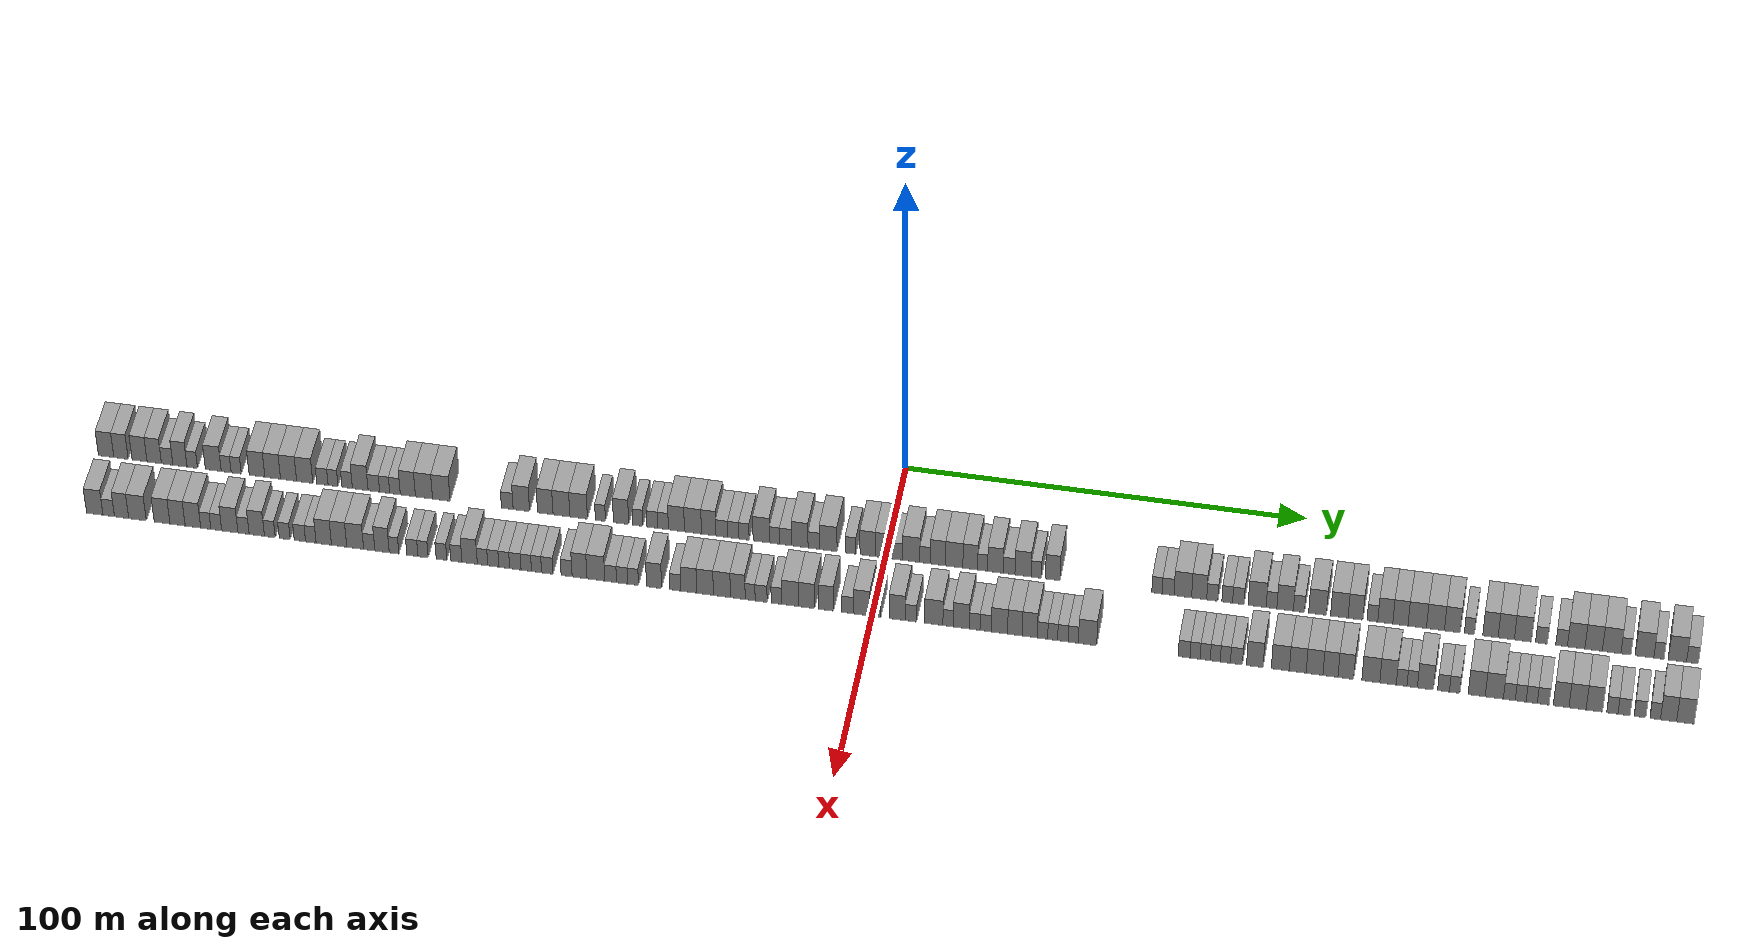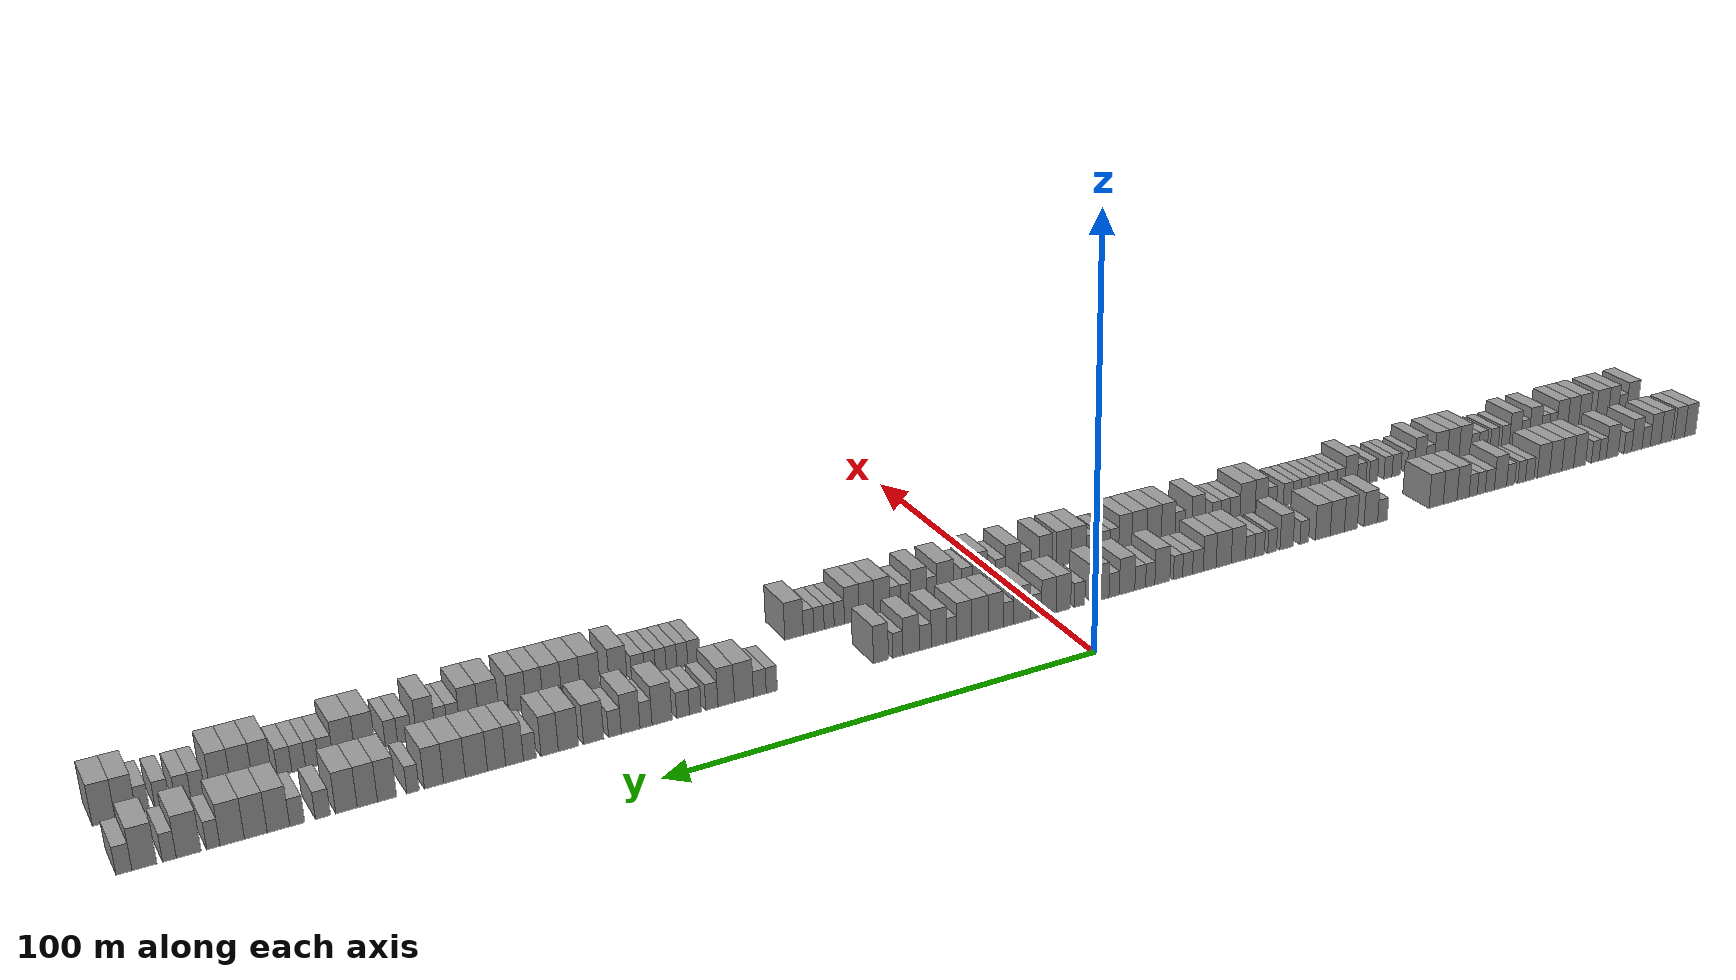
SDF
<sdf version="1.6">
 <world name="default">
  <scene>
   <sky><clouds><speed>12</speed></clouds></sky>
   <ambient>0.4 0.4 0.4 1</ambient>
   <background>0.7 0.7 0.7 1</background>
   <shadows>1</shadows>
  </scene>
  <gravity>0 0 -9.8066</gravity>
  <magnetic_field>6e-06 2.3e-05 -4.2e-05</magnetic_field>
  <physics default="0" name="default_physics" type="ode">
   <ode>
    <solver>
     <type>quick</type>
     <iters>10</iters>
     <sor>1.0</sor>
     <use_dynamic_moi_rescaling>0</use_dynamic_moi_rescaling>
    </solver>
    <constraints>
     <cfm>0</cfm>
     <erp>0.2</erp>
     <contact_max_correcting_vel>100</contact_max_correcting_vel>
     <contact_surface_layer>0.001</contact_surface_layer>
    </constraints>
   </ode>
   <max_step_size>0.004</max_step_size>
   <real_time_factor>1</real_time_factor>
   <real_time_update_rate>250</real_time_update_rate>
  </physics>
  <light name="sun" type="directional">
   <pose>0 0 10 0 0 0</pose>
   <diffuse>0.8 0.8 0.8 1</diffuse>
   <specular>0.2 0.2 0.2 1</specular>
   <attenuation>
    <range>1000</range>
    <constant>0.9</constant>
    <linear>0.01</linear>
    <quadratic>0.001</quadratic>
   </attenuation>
   <direction>-0.5 0.1 -0.9</direction>
  </light>
  <model name="building_1">
   <static>1</static>
   <pose>25.0000 -196.0314 0 0.000000 0.000000 0.000000</pose>
   <link name="link">
    <pose>0 0 4.50 0 0 0</pose>
    <collision name="collision"><geometry><box><size>10.0000 3.9372 9.0000</size></box></geometry></collision>
    <visual name="visual">
     <cast_shadows>0</cast_shadows>
     <geometry><box><size>10.0000 3.9372 9.0000</size></box></geometry>
     <material>
      <script>
       <uri>model://grey_wall/materials/scripts</uri>
       <uri>model://grey_wall/materials/textures</uri>
       <name>vrc/grey_wall</name>
      </script>
     </material>
    </visual>
   </link>
  </model>
  <model name="building_2">
   <static>1</static>
   <pose>25.0000 -192.2365 0 0.000000 0.000000 0.000000</pose>
   <link name="link">
    <pose>0 0 4.50 0 0 0</pose>
    <collision name="collision"><geometry><box><size>10.0000 3.6526 9.0000</size></box></geometry></collision>
    <visual name="visual">
     <cast_shadows>0</cast_shadows>
     <geometry><box><size>10.0000 3.6526 9.0000</size></box></geometry>
     <material>
      <script>
       <uri>model://grey_wall/materials/scripts</uri>
       <uri>model://grey_wall/materials/textures</uri>
       <name>vrc/grey_wall</name>
      </script>
     </material>
    </visual>
   </link>
  </model>
  <model name="building_3">
   <static>1</static>
   <pose>25.0000 -187.5017 0 0.000000 0.000000 0.000000</pose>
   <link name="link">
    <pose>0 0 4.50 0 0 0</pose>
    <collision name="collision"><geometry><box><size>10.0000 3.8169 9.0000</size></box></geometry></collision>
    <visual name="visual">
     <cast_shadows>0</cast_shadows>
     <geometry><box><size>10.0000 3.8169 9.0000</size></box></geometry>
     <material>
      <script>
       <uri>model://grey_wall/materials/scripts</uri>
       <uri>model://grey_wall/materials/textures</uri>
       <name>vrc/grey_wall</name>
      </script>
     </material>
    </visual>
   </link>
  </model>
  <model name="building_4">
   <static>1</static>
   <pose>25.0000 -183.7541 0 0.000000 0.000000 0.000000</pose>
   <link name="link">
    <pose>0 0 4.50 0 0 0</pose>
    <collision name="collision"><geometry><box><size>10.0000 3.6784 9.0000</size></box></geometry></collision>
    <visual name="visual">
     <cast_shadows>0</cast_shadows>
     <geometry><box><size>10.0000 3.6784 9.0000</size></box></geometry>
     <material>
      <script>
       <uri>model://grey_wall/materials/scripts</uri>
       <uri>model://grey_wall/materials/textures</uri>
       <name>vrc/grey_wall</name>
      </script>
     </material>
    </visual>
   </link>
  </model>
  <model name="building_5">
   <static>1</static>
   <pose>25.0000 -180.4640 0 0.000000 0.000000 0.000000</pose>
   <link name="link">
    <pose>0 0 3.00 0 0 0</pose>
    <collision name="collision"><geometry><box><size>10.0000 2.9017 6.0000</size></box></geometry></collision>
    <visual name="visual">
     <cast_shadows>0</cast_shadows>
     <geometry><box><size>10.0000 2.9017 6.0000</size></box></geometry>
     <material>
      <script>
       <uri>model://grey_wall/materials/scripts</uri>
       <uri>model://grey_wall/materials/textures</uri>
       <name>vrc/grey_wall</name>
      </script>
     </material>
    </visual>
   </link>
  </model>
  <model name="building_6">
   <static>1</static>
   <pose>25.0000 -177.2093 0 0.000000 0.000000 0.000000</pose>
   <link name="link">
    <pose>0 0 4.50 0 0 0</pose>
    <collision name="collision"><geometry><box><size>10.0000 3.6077 9.0000</size></box></geometry></collision>
    <visual name="visual">
     <cast_shadows>0</cast_shadows>
     <geometry><box><size>10.0000 3.6077 9.0000</size></box></geometry>
     <material>
      <script>
       <uri>model://grey_wall/materials/scripts</uri>
       <uri>model://grey_wall/materials/textures</uri>
       <name>vrc/grey_wall</name>
      </script>
     </material>
    </visual>
   </link>
  </model>
  <model name="building_7">
   <static>1</static>
   <pose>25.0000 -174.0762 0 0.000000 0.000000 0.000000</pose>
   <link name="link">
    <pose>0 0 3.00 0 0 0</pose>
    <collision name="collision"><geometry><box><size>10.0000 2.6586 6.0000</size></box></geometry></collision>
    <visual name="visual">
     <cast_shadows>0</cast_shadows>
     <geometry><box><size>10.0000 2.6586 6.0000</size></box></geometry>
     <material>
      <script>
       <uri>model://grey_wall/materials/scripts</uri>
       <uri>model://grey_wall/materials/textures</uri>
       <name>vrc/grey_wall</name>
      </script>
     </material>
    </visual>
   </link>
  </model>
  <model name="building_8">
   <static>1</static>
   <pose>25.0000 -168.7161 0 0.000000 0.000000 0.000000</pose>
   <link name="link">
    <pose>0 0 4.50 0 0 0</pose>
    <collision name="collision"><geometry><box><size>10.0000 4.0615 9.0000</size></box></geometry></collision>
    <visual name="visual">
     <cast_shadows>0</cast_shadows>
     <geometry><box><size>10.0000 4.0615 9.0000</size></box></geometry>
     <material>
      <script>
       <uri>model://grey_wall/materials/scripts</uri>
       <uri>model://grey_wall/materials/textures</uri>
       <name>vrc/grey_wall</name>
      </script>
     </material>
    </visual>
   </link>
  </model>
  <model name="building_9">
   <static>1</static>
   <pose>25.0000 -165.4350 0 0.000000 0.000000 0.000000</pose>
   <link name="link">
    <pose>0 0 3.00 0 0 0</pose>
    <collision name="collision"><geometry><box><size>10.0000 2.5007 6.0000</size></box></geometry></collision>
    <visual name="visual">
     <cast_shadows>0</cast_shadows>
     <geometry><box><size>10.0000 2.5007 6.0000</size></box></geometry>
     <material>
      <script>
       <uri>model://grey_wall/materials/scripts</uri>
       <uri>model://grey_wall/materials/textures</uri>
       <name>vrc/grey_wall</name>
      </script>
     </material>
    </visual>
   </link>
  </model>
  <model name="building_10">
   <static>1</static>
   <pose>25.0000 -162.8917 0 0.000000 0.000000 0.000000</pose>
   <link name="link">
    <pose>0 0 3.00 0 0 0</pose>
    <collision name="collision"><geometry><box><size>10.0000 2.5860 6.0000</size></box></geometry></collision>
    <visual name="visual">
     <cast_shadows>0</cast_shadows>
     <geometry><box><size>10.0000 2.5860 6.0000</size></box></geometry>
     <material>
      <script>
       <uri>model://grey_wall/materials/scripts</uri>
       <uri>model://grey_wall/materials/textures</uri>
       <name>vrc/grey_wall</name>
      </script>
     </material>
    </visual>
   </link>
  </model>
  <model name="building_11">
   <static>1</static>
   <pose>25.0000 -157.6022 0 0.000000 0.000000 0.000000</pose>
   <link name="link">
    <pose>0 0 4.50 0 0 0</pose>
    <collision name="collision"><geometry><box><size>10.0000 3.9928 9.0000</size></box></geometry></collision>
    <visual name="visual">
     <cast_shadows>0</cast_shadows>
     <geometry><box><size>10.0000 3.9928 9.0000</size></box></geometry>
     <material>
      <script>
       <uri>model://grey_wall/materials/scripts</uri>
       <uri>model://grey_wall/materials/textures</uri>
       <name>vrc/grey_wall</name>
      </script>
     </material>
    </visual>
   </link>
  </model>
  <model name="building_12">
   <static>1</static>
   <pose>25.0000 -153.6152 0 0.000000 0.000000 0.000000</pose>
   <link name="link">
    <pose>0 0 4.50 0 0 0</pose>
    <collision name="collision"><geometry><box><size>10.0000 3.9812 9.0000</size></box></geometry></collision>
    <visual name="visual">
     <cast_shadows>0</cast_shadows>
     <geometry><box><size>10.0000 3.9812 9.0000</size></box></geometry>
     <material>
      <script>
       <uri>model://grey_wall/materials/scripts</uri>
       <uri>model://grey_wall/materials/textures</uri>
       <name>vrc/grey_wall</name>
      </script>
     </material>
    </visual>
   </link>
  </model>
  <model name="building_13">
   <static>1</static>
   <pose>25.0000 -149.5801 0 0.000000 0.000000 0.000000</pose>
   <link name="link">
    <pose>0 0 4.50 0 0 0</pose>
    <collision name="collision"><geometry><box><size>10.0000 4.0890 9.0000</size></box></geometry></collision>
    <visual name="visual">
     <cast_shadows>0</cast_shadows>
     <geometry><box><size>10.0000 4.0890 9.0000</size></box></geometry>
     <material>
      <script>
       <uri>model://grey_wall/materials/scripts</uri>
       <uri>model://grey_wall/materials/textures</uri>
       <name>vrc/grey_wall</name>
      </script>
     </material>
    </visual>
   </link>
  </model>
  <model name="building_14">
   <static>1</static>
   <pose>25.0000 -145.4824 0 0.000000 0.000000 0.000000</pose>
   <link name="link">
    <pose>0 0 4.50 0 0 0</pose>
    <collision name="collision"><geometry><box><size>10.0000 4.1064 9.0000</size></box></geometry></collision>
    <visual name="visual">
     <cast_shadows>0</cast_shadows>
     <geometry><box><size>10.0000 4.1064 9.0000</size></box></geometry>
     <material>
      <script>
       <uri>model://grey_wall/materials/scripts</uri>
       <uri>model://grey_wall/materials/textures</uri>
       <name>vrc/grey_wall</name>
      </script>
     </material>
    </visual>
   </link>
  </model>
  <model name="building_15">
   <static>1</static>
   <pose>25.0000 -140.9967 0 0.000000 0.000000 0.000000</pose>
   <link name="link">
    <pose>0 0 3.00 0 0 0</pose>
    <collision name="collision"><geometry><box><size>10.0000 2.8648 6.0000</size></box></geometry></collision>
    <visual name="visual">
     <cast_shadows>0</cast_shadows>
     <geometry><box><size>10.0000 2.8648 6.0000</size></box></geometry>
     <material>
      <script>
       <uri>model://grey_wall/materials/scripts</uri>
       <uri>model://grey_wall/materials/textures</uri>
       <name>vrc/grey_wall</name>
      </script>
     </material>
    </visual>
   </link>
  </model>
  <model name="building_16">
   <static>1</static>
   <pose>25.0000 -138.3111 0 0.000000 0.000000 0.000000</pose>
   <link name="link">
    <pose>0 0 3.00 0 0 0</pose>
    <collision name="collision"><geometry><box><size>10.0000 2.5065 6.0000</size></box></geometry></collision>
    <visual name="visual">
     <cast_shadows>0</cast_shadows>
     <geometry><box><size>10.0000 2.5065 6.0000</size></box></geometry>
     <material>
      <script>
       <uri>model://grey_wall/materials/scripts</uri>
       <uri>model://grey_wall/materials/textures</uri>
       <name>vrc/grey_wall</name>
      </script>
     </material>
    </visual>
   </link>
  </model>
  <model name="building_17">
   <static>1</static>
   <pose>25.0000 -134.7319 0 0.000000 0.000000 0.000000</pose>
   <link name="link">
    <pose>0 0 3.00 0 0 0</pose>
    <collision name="collision"><geometry><box><size>10.0000 2.6518 6.0000</size></box></geometry></collision>
    <visual name="visual">
     <cast_shadows>0</cast_shadows>
     <geometry><box><size>10.0000 2.6518 6.0000</size></box></geometry>
     <material>
      <script>
       <uri>model://grey_wall/materials/scripts</uri>
       <uri>model://grey_wall/materials/textures</uri>
       <name>vrc/grey_wall</name>
      </script>
     </material>
    </visual>
   </link>
  </model>
  <model name="building_18">
   <static>1</static>
   <pose>25.0000 -131.4228 0 0.000000 0.000000 0.000000</pose>
   <link name="link">
    <pose>0 0 4.50 0 0 0</pose>
    <collision name="collision"><geometry><box><size>10.0000 3.9664 9.0000</size></box></geometry></collision>
    <visual name="visual">
     <cast_shadows>0</cast_shadows>
     <geometry><box><size>10.0000 3.9664 9.0000</size></box></geometry>
     <material>
      <script>
       <uri>model://grey_wall/materials/scripts</uri>
       <uri>model://grey_wall/materials/textures</uri>
       <name>vrc/grey_wall</name>
      </script>
     </material>
    </visual>
   </link>
  </model>
  <model name="building_19">
   <static>1</static>
   <pose>25.0000 -127.9781 0 0.000000 0.000000 0.000000</pose>
   <link name="link">
    <pose>0 0 3.00 0 0 0</pose>
    <collision name="collision"><geometry><box><size>10.0000 2.9230 6.0000</size></box></geometry></collision>
    <visual name="visual">
     <cast_shadows>0</cast_shadows>
     <geometry><box><size>10.0000 2.9230 6.0000</size></box></geometry>
     <material>
      <script>
       <uri>model://grey_wall/materials/scripts</uri>
       <uri>model://grey_wall/materials/textures</uri>
       <name>vrc/grey_wall</name>
      </script>
     </material>
    </visual>
   </link>
  </model>
  <model name="building_20">
   <static>1</static>
   <pose>25.0000 -125.2448 0 0.000000 0.000000 0.000000</pose>
   <link name="link">
    <pose>0 0 3.00 0 0 0</pose>
    <collision name="collision"><geometry><box><size>10.0000 2.5437 6.0000</size></box></geometry></collision>
    <visual name="visual">
     <cast_shadows>0</cast_shadows>
     <geometry><box><size>10.0000 2.5437 6.0000</size></box></geometry>
     <material>
      <script>
       <uri>model://grey_wall/materials/scripts</uri>
       <uri>model://grey_wall/materials/textures</uri>
       <name>vrc/grey_wall</name>
      </script>
     </material>
    </visual>
   </link>
  </model>
  <model name="building_21">
   <static>1</static>
   <pose>25.0000 -122.6416 0 0.000000 0.000000 0.000000</pose>
   <link name="link">
    <pose>0 0 3.00 0 0 0</pose>
    <collision name="collision"><geometry><box><size>10.0000 2.6627 6.0000</size></box></geometry></collision>
    <visual name="visual">
     <cast_shadows>0</cast_shadows>
     <geometry><box><size>10.0000 2.6627 6.0000</size></box></geometry>
     <material>
      <script>
       <uri>model://grey_wall/materials/scripts</uri>
       <uri>model://grey_wall/materials/textures</uri>
       <name>vrc/grey_wall</name>
      </script>
     </material>
    </visual>
   </link>
  </model>
  <model name="building_22">
   <static>1</static>
   <pose>25.0000 -119.3938 0 0.000000 0.000000 0.000000</pose>
   <link name="link">
    <pose>0 0 4.50 0 0 0</pose>
    <collision name="collision"><geometry><box><size>10.0000 3.8329 9.0000</size></box></geometry></collision>
    <visual name="visual">
     <cast_shadows>0</cast_shadows>
     <geometry><box><size>10.0000 3.8329 9.0000</size></box></geometry>
     <material>
      <script>
       <uri>model://grey_wall/materials/scripts</uri>
       <uri>model://grey_wall/materials/textures</uri>
       <name>vrc/grey_wall</name>
      </script>
     </material>
    </visual>
   </link>
  </model>
  <model name="building_23">
   <static>1</static>
   <pose>25.0000 -115.3170 0 0.000000 0.000000 0.000000</pose>
   <link name="link">
    <pose>0 0 4.50 0 0 0</pose>
    <collision name="collision"><geometry><box><size>10.0000 4.3206 9.0000</size></box></geometry></collision>
    <visual name="visual">
     <cast_shadows>0</cast_shadows>
     <geometry><box><size>10.0000 4.3206 9.0000</size></box></geometry>
     <material>
      <script>
       <uri>model://grey_wall/materials/scripts</uri>
       <uri>model://grey_wall/materials/textures</uri>
       <name>vrc/grey_wall</name>
      </script>
     </material>
    </visual>
   </link>
  </model>
  <model name="building_24">
   <static>1</static>
   <pose>25.0000 -110.9429 0 0.000000 0.000000 0.000000</pose>
   <link name="link">
    <pose>0 0 4.50 0 0 0</pose>
    <collision name="collision"><geometry><box><size>10.0000 4.4276 9.0000</size></box></geometry></collision>
    <visual name="visual">
     <cast_shadows>0</cast_shadows>
     <geometry><box><size>10.0000 4.4276 9.0000</size></box></geometry>
     <material>
      <script>
       <uri>model://grey_wall/materials/scripts</uri>
       <uri>model://grey_wall/materials/textures</uri>
       <name>vrc/grey_wall</name>
      </script>
     </material>
    </visual>
   </link>
  </model>
  <model name="building_25">
   <static>1</static>
   <pose>25.0000 -94.3195 0 0.000000 0.000000 0.000000</pose>
   <link name="link">
    <pose>0 0 3.00 0 0 0</pose>
    <collision name="collision"><geometry><box><size>10.0000 2.9398 6.0000</size></box></geometry></collision>
    <visual name="visual">
     <cast_shadows>0</cast_shadows>
     <geometry><box><size>10.0000 2.9398 6.0000</size></box></geometry>
     <material>
      <script>
       <uri>model://grey_wall/materials/scripts</uri>
       <uri>model://grey_wall/materials/textures</uri>
       <name>vrc/grey_wall</name>
      </script>
     </material>
    </visual>
   </link>
  </model>
  <model name="building_26">
   <static>1</static>
   <pose>25.0000 -90.7774 0 0.000000 0.000000 0.000000</pose>
   <link name="link">
    <pose>0 0 4.50 0 0 0</pose>
    <collision name="collision"><geometry><box><size>10.0000 4.1444 9.0000</size></box></geometry></collision>
    <visual name="visual">
     <cast_shadows>0</cast_shadows>
     <geometry><box><size>10.0000 4.1444 9.0000</size></box></geometry>
     <material>
      <script>
       <uri>model://grey_wall/materials/scripts</uri>
       <uri>model://grey_wall/materials/textures</uri>
       <name>vrc/grey_wall</name>
      </script>
     </material>
    </visual>
   </link>
  </model>
  <model name="building_27">
   <static>1</static>
   <pose>25.0000 -84.7601 0 0.000000 0.000000 0.000000</pose>
   <link name="link">
    <pose>0 0 4.50 0 0 0</pose>
    <collision name="collision"><geometry><box><size>10.0000 3.8902 9.0000</size></box></geometry></collision>
    <visual name="visual">
     <cast_shadows>0</cast_shadows>
     <geometry><box><size>10.0000 3.8902 9.0000</size></box></geometry>
     <material>
      <script>
       <uri>model://grey_wall/materials/scripts</uri>
       <uri>model://grey_wall/materials/textures</uri>
       <name>vrc/grey_wall</name>
      </script>
     </material>
    </visual>
   </link>
  </model>
  <model name="building_28">
   <static>1</static>
   <pose>25.0000 -80.6987 0 0.000000 0.000000 0.000000</pose>
   <link name="link">
    <pose>0 0 4.50 0 0 0</pose>
    <collision name="collision"><geometry><box><size>10.0000 4.2326 9.0000</size></box></geometry></collision>
    <visual name="visual">
     <cast_shadows>0</cast_shadows>
     <geometry><box><size>10.0000 4.2326 9.0000</size></box></geometry>
     <material>
      <script>
       <uri>model://grey_wall/materials/scripts</uri>
       <uri>model://grey_wall/materials/textures</uri>
       <name>vrc/grey_wall</name>
      </script>
     </material>
    </visual>
   </link>
  </model>
  <model name="building_29">
   <static>1</static>
   <pose>25.0000 -76.3825 0 0.000000 0.000000 0.000000</pose>
   <link name="link">
    <pose>0 0 4.50 0 0 0</pose>
    <collision name="collision"><geometry><box><size>10.0000 4.3999 9.0000</size></box></geometry></collision>
    <visual name="visual">
     <cast_shadows>0</cast_shadows>
     <geometry><box><size>10.0000 4.3999 9.0000</size></box></geometry>
     <material>
      <script>
       <uri>model://grey_wall/materials/scripts</uri>
       <uri>model://grey_wall/materials/textures</uri>
       <name>vrc/grey_wall</name>
      </script>
     </material>
    </visual>
   </link>
  </model>
  <model name="building_30">
   <static>1</static>
   <pose>25.0000 -70.9195 0 0.000000 0.000000 0.000000</pose>
   <link name="link">
    <pose>0 0 3.00 0 0 0</pose>
    <collision name="collision"><geometry><box><size>10.0000 2.5261 6.0000</size></box></geometry></collision>
    <visual name="visual">
     <cast_shadows>0</cast_shadows>
     <geometry><box><size>10.0000 2.5261 6.0000</size></box></geometry>
     <material>
      <script>
       <uri>model://grey_wall/materials/scripts</uri>
       <uri>model://grey_wall/materials/textures</uri>
       <name>vrc/grey_wall</name>
      </script>
     </material>
    </visual>
   </link>
  </model>
  <model name="building_31">
   <static>1</static>
   <pose>25.0000 -65.7433 0 0.000000 0.000000 0.000000</pose>
   <link name="link">
    <pose>0 0 4.50 0 0 0</pose>
    <collision name="collision"><geometry><box><size>10.0000 3.8264 9.0000</size></box></geometry></collision>
    <visual name="visual">
     <cast_shadows>0</cast_shadows>
     <geometry><box><size>10.0000 3.8264 9.0000</size></box></geometry>
     <material>
      <script>
       <uri>model://grey_wall/materials/scripts</uri>
       <uri>model://grey_wall/materials/textures</uri>
       <name>vrc/grey_wall</name>
      </script>
     </material>
    </visual>
   </link>
  </model>
  <model name="building_32">
   <static>1</static>
   <pose>25.0000 -61.5721 0 0.000000 0.000000 0.000000</pose>
   <link name="link">
    <pose>0 0 3.00 0 0 0</pose>
    <collision name="collision"><geometry><box><size>10.0000 2.5161 6.0000</size></box></geometry></collision>
    <visual name="visual">
     <cast_shadows>0</cast_shadows>
     <geometry><box><size>10.0000 2.5161 6.0000</size></box></geometry>
     <material>
      <script>
       <uri>model://grey_wall/materials/scripts</uri>
       <uri>model://grey_wall/materials/textures</uri>
       <name>vrc/grey_wall</name>
      </script>
     </material>
    </visual>
   </link>
  </model>
  <model name="building_33">
   <static>1</static>
   <pose>25.0000 -57.9452 0 0.000000 0.000000 0.000000</pose>
   <link name="link">
    <pose>0 0 3.00 0 0 0</pose>
    <collision name="collision"><geometry><box><size>10.0000 2.7375 6.0000</size></box></geometry></collision>
    <visual name="visual">
     <cast_shadows>0</cast_shadows>
     <geometry><box><size>10.0000 2.7375 6.0000</size></box></geometry>
     <material>
      <script>
       <uri>model://grey_wall/materials/scripts</uri>
       <uri>model://grey_wall/materials/textures</uri>
       <name>vrc/grey_wall</name>
      </script>
     </material>
    </visual>
   </link>
  </model>
  <model name="building_34">
   <static>1</static>
   <pose>25.0000 -55.2380 0 0.000000 0.000000 0.000000</pose>
   <link name="link">
    <pose>0 0 3.00 0 0 0</pose>
    <collision name="collision"><geometry><box><size>10.0000 2.6770 6.0000</size></box></geometry></collision>
    <visual name="visual">
     <cast_shadows>0</cast_shadows>
     <geometry><box><size>10.0000 2.6770 6.0000</size></box></geometry>
     <material>
      <script>
       <uri>model://grey_wall/materials/scripts</uri>
       <uri>model://grey_wall/materials/textures</uri>
       <name>vrc/grey_wall</name>
      </script>
     </material>
    </visual>
   </link>
  </model>
  <model name="building_35">
   <static>1</static>
   <pose>25.0000 -51.8921 0 0.000000 0.000000 0.000000</pose>
   <link name="link">
    <pose>0 0 4.50 0 0 0</pose>
    <collision name="collision"><geometry><box><size>10.0000 4.0147 9.0000</size></box></geometry></collision>
    <visual name="visual">
     <cast_shadows>0</cast_shadows>
     <geometry><box><size>10.0000 4.0147 9.0000</size></box></geometry>
     <material>
      <script>
       <uri>model://grey_wall/materials/scripts</uri>
       <uri>model://grey_wall/materials/textures</uri>
       <name>vrc/grey_wall</name>
      </script>
     </material>
    </visual>
   </link>
  </model>
  <model name="building_36">
   <static>1</static>
   <pose>25.0000 -47.7623 0 0.000000 0.000000 0.000000</pose>
   <link name="link">
    <pose>0 0 4.50 0 0 0</pose>
    <collision name="collision"><geometry><box><size>10.0000 4.2450 9.0000</size></box></geometry></collision>
    <visual name="visual">
     <cast_shadows>0</cast_shadows>
     <geometry><box><size>10.0000 4.2450 9.0000</size></box></geometry>
     <material>
      <script>
       <uri>model://grey_wall/materials/scripts</uri>
       <uri>model://grey_wall/materials/textures</uri>
       <name>vrc/grey_wall</name>
      </script>
     </material>
    </visual>
   </link>
  </model>
  <model name="building_37">
   <static>1</static>
   <pose>25.0000 -43.8345 0 0.000000 0.000000 0.000000</pose>
   <link name="link">
    <pose>0 0 4.50 0 0 0</pose>
    <collision name="collision"><geometry><box><size>10.0000 3.6106 9.0000</size></box></geometry></collision>
    <visual name="visual">
     <cast_shadows>0</cast_shadows>
     <geometry><box><size>10.0000 3.6106 9.0000</size></box></geometry>
     <material>
      <script>
       <uri>model://grey_wall/materials/scripts</uri>
       <uri>model://grey_wall/materials/textures</uri>
       <name>vrc/grey_wall</name>
      </script>
     </material>
    </visual>
   </link>
  </model>
  <model name="building_38">
   <static>1</static>
   <pose>25.0000 -40.5344 0 0.000000 0.000000 0.000000</pose>
   <link name="link">
    <pose>0 0 3.00 0 0 0</pose>
    <collision name="collision"><geometry><box><size>10.0000 2.9896 6.0000</size></box></geometry></collision>
    <visual name="visual">
     <cast_shadows>0</cast_shadows>
     <geometry><box><size>10.0000 2.9896 6.0000</size></box></geometry>
     <material>
      <script>
       <uri>model://grey_wall/materials/scripts</uri>
       <uri>model://grey_wall/materials/textures</uri>
       <name>vrc/grey_wall</name>
      </script>
     </material>
    </visual>
   </link>
  </model>
  <model name="building_39">
   <static>1</static>
   <pose>25.0000 -37.6653 0 0.000000 0.000000 0.000000</pose>
   <link name="link">
    <pose>0 0 3.00 0 0 0</pose>
    <collision name="collision"><geometry><box><size>10.0000 2.7485 6.0000</size></box></geometry></collision>
    <visual name="visual">
     <cast_shadows>0</cast_shadows>
     <geometry><box><size>10.0000 2.7485 6.0000</size></box></geometry>
     <material>
      <script>
       <uri>model://grey_wall/materials/scripts</uri>
       <uri>model://grey_wall/materials/textures</uri>
       <name>vrc/grey_wall</name>
      </script>
     </material>
    </visual>
   </link>
  </model>
  <model name="building_40">
   <static>1</static>
   <pose>25.0000 -35.0233 0 0.000000 0.000000 0.000000</pose>
   <link name="link">
    <pose>0 0 3.00 0 0 0</pose>
    <collision name="collision"><geometry><box><size>10.0000 2.5355 6.0000</size></box></geometry></collision>
    <visual name="visual">
     <cast_shadows>0</cast_shadows>
     <geometry><box><size>10.0000 2.5355 6.0000</size></box></geometry>
     <material>
      <script>
       <uri>model://grey_wall/materials/scripts</uri>
       <uri>model://grey_wall/materials/textures</uri>
       <name>vrc/grey_wall</name>
      </script>
     </material>
    </visual>
   </link>
  </model>
  <model name="building_41">
   <static>1</static>
   <pose>25.0000 -30.7045 0 0.000000 0.000000 0.000000</pose>
   <link name="link">
    <pose>0 0 4.50 0 0 0</pose>
    <collision name="collision"><geometry><box><size>10.0000 4.1022 9.0000</size></box></geometry></collision>
    <visual name="visual">
     <cast_shadows>0</cast_shadows>
     <geometry><box><size>10.0000 4.1022 9.0000</size></box></geometry>
     <material>
      <script>
       <uri>model://grey_wall/materials/scripts</uri>
       <uri>model://grey_wall/materials/textures</uri>
       <name>vrc/grey_wall</name>
      </script>
     </material>
    </visual>
   </link>
  </model>
  <model name="building_42">
   <static>1</static>
   <pose>25.0000 -27.3990 0 0.000000 0.000000 0.000000</pose>
   <link name="link">
    <pose>0 0 3.00 0 0 0</pose>
    <collision name="collision"><geometry><box><size>10.0000 2.5086 6.0000</size></box></geometry></collision>
    <visual name="visual">
     <cast_shadows>0</cast_shadows>
     <geometry><box><size>10.0000 2.5086 6.0000</size></box></geometry>
     <material>
      <script>
       <uri>model://grey_wall/materials/scripts</uri>
       <uri>model://grey_wall/materials/textures</uri>
       <name>vrc/grey_wall</name>
      </script>
     </material>
    </visual>
   </link>
  </model>
  <model name="building_43">
   <static>1</static>
   <pose>25.0000 -24.6789 0 0.000000 0.000000 0.000000</pose>
   <link name="link">
    <pose>0 0 3.00 0 0 0</pose>
    <collision name="collision"><geometry><box><size>10.0000 2.9316 6.0000</size></box></geometry></collision>
    <visual name="visual">
     <cast_shadows>0</cast_shadows>
     <geometry><box><size>10.0000 2.9316 6.0000</size></box></geometry>
     <material>
      <script>
       <uri>model://grey_wall/materials/scripts</uri>
       <uri>model://grey_wall/materials/textures</uri>
       <name>vrc/grey_wall</name>
      </script>
     </material>
    </visual>
   </link>
  </model>
  <model name="building_44">
   <static>1</static>
   <pose>25.0000 -21.1444 0 0.000000 0.000000 0.000000</pose>
   <link name="link">
    <pose>0 0 4.50 0 0 0</pose>
    <collision name="collision"><geometry><box><size>10.0000 4.1376 9.0000</size></box></geometry></collision>
    <visual name="visual">
     <cast_shadows>0</cast_shadows>
     <geometry><box><size>10.0000 4.1376 9.0000</size></box></geometry>
     <material>
      <script>
       <uri>model://grey_wall/materials/scripts</uri>
       <uri>model://grey_wall/materials/textures</uri>
       <name>vrc/grey_wall</name>
      </script>
     </material>
    </visual>
   </link>
  </model>
  <model name="building_45">
   <static>1</static>
   <pose>25.0000 -17.6661 0 0.000000 0.000000 0.000000</pose>
   <link name="link">
    <pose>0 0 3.00 0 0 0</pose>
    <collision name="collision"><geometry><box><size>10.0000 2.8188 6.0000</size></box></geometry></collision>
    <visual name="visual">
     <cast_shadows>0</cast_shadows>
     <geometry><box><size>10.0000 2.8188 6.0000</size></box></geometry>
     <material>
      <script>
       <uri>model://grey_wall/materials/scripts</uri>
       <uri>model://grey_wall/materials/textures</uri>
       <name>vrc/grey_wall</name>
      </script>
     </material>
    </visual>
   </link>
  </model>
  <model name="building_46">
   <static>1</static>
   <pose>25.0000 -14.0610 0 0.000000 0.000000 0.000000</pose>
   <link name="link">
    <pose>0 0 4.50 0 0 0</pose>
    <collision name="collision"><geometry><box><size>10.0000 4.3914 9.0000</size></box></geometry></collision>
    <visual name="visual">
     <cast_shadows>0</cast_shadows>
     <geometry><box><size>10.0000 4.3914 9.0000</size></box></geometry>
     <material>
      <script>
       <uri>model://grey_wall/materials/scripts</uri>
       <uri>model://grey_wall/materials/textures</uri>
       <name>vrc/grey_wall</name>
      </script>
     </material>
    </visual>
   </link>
  </model>
  <model name="building_47">
   <static>1</static>
   <pose>25.0000 -8.5152 0 0.000000 0.000000 0.000000</pose>
   <link name="link">
    <pose>0 0 3.00 0 0 0</pose>
    <collision name="collision"><geometry><box><size>10.0000 2.7003 6.0000</size></box></geometry></collision>
    <visual name="visual">
     <cast_shadows>0</cast_shadows>
     <geometry><box><size>10.0000 2.7003 6.0000</size></box></geometry>
     <material>
      <script>
       <uri>model://grey_wall/materials/scripts</uri>
       <uri>model://grey_wall/materials/textures</uri>
       <name>vrc/grey_wall</name>
      </script>
     </material>
    </visual>
   </link>
  </model>
  <model name="building_48">
   <static>1</static>
   <pose>25.0000 -4.2827 0 0.000000 0.000000 0.000000</pose>
   <link name="link">
    <pose>0 0 4.50 0 0 0</pose>
    <collision name="collision"><geometry><box><size>10.0000 3.7647 9.0000</size></box></geometry></collision>
    <visual name="visual">
     <cast_shadows>0</cast_shadows>
     <geometry><box><size>10.0000 3.7647 9.0000</size></box></geometry>
     <material>
      <script>
       <uri>model://grey_wall/materials/scripts</uri>
       <uri>model://grey_wall/materials/textures</uri>
       <name>vrc/grey_wall</name>
      </script>
     </material>
    </visual>
   </link>
  </model>
  <model name="building_49">
   <static>1</static>
   <pose>25.0000 -0.5022 0 0.000000 0.000000 0.000000</pose>
   <link name="link">
    <pose>0 0 4.50 0 0 0</pose>
    <collision name="collision"><geometry><box><size>10.0000 3.7964 9.0000</size></box></geometry></collision>
    <visual name="visual">
     <cast_shadows>0</cast_shadows>
     <geometry><box><size>10.0000 3.7964 9.0000</size></box></geometry>
     <material>
      <script>
       <uri>model://grey_wall/materials/scripts</uri>
       <uri>model://grey_wall/materials/textures</uri>
       <name>vrc/grey_wall</name>
      </script>
     </material>
    </visual>
   </link>
  </model>
  <model name="building_50">
   <static>1</static>
   <pose>25.0000 2.8793 0 0.000000 0.000000 0.000000</pose>
   <link name="link">
    <pose>0 0 3.00 0 0 0</pose>
    <collision name="collision"><geometry><box><size>10.0000 2.9666 6.0000</size></box></geometry></collision>
    <visual name="visual">
     <cast_shadows>0</cast_shadows>
     <geometry><box><size>10.0000 2.9666 6.0000</size></box></geometry>
     <material>
      <script>
       <uri>model://grey_wall/materials/scripts</uri>
       <uri>model://grey_wall/materials/textures</uri>
       <name>vrc/grey_wall</name>
      </script>
     </material>
    </visual>
   </link>
  </model>
  <model name="building_51">
   <static>1</static>
   <pose>25.0000 6.5234 0 0.000000 0.000000 0.000000</pose>
   <link name="link">
    <pose>0 0 4.50 0 0 0</pose>
    <collision name="collision"><geometry><box><size>10.0000 4.3214 9.0000</size></box></geometry></collision>
    <visual name="visual">
     <cast_shadows>0</cast_shadows>
     <geometry><box><size>10.0000 4.3214 9.0000</size></box></geometry>
     <material>
      <script>
       <uri>model://grey_wall/materials/scripts</uri>
       <uri>model://grey_wall/materials/textures</uri>
       <name>vrc/grey_wall</name>
      </script>
     </material>
    </visual>
   </link>
  </model>
  <model name="building_52">
   <static>1</static>
   <pose>25.0000 9.9989 0 0.000000 0.000000 0.000000</pose>
   <link name="link">
    <pose>0 0 3.00 0 0 0</pose>
    <collision name="collision"><geometry><box><size>10.0000 2.6296 6.0000</size></box></geometry></collision>
    <visual name="visual">
     <cast_shadows>0</cast_shadows>
     <geometry><box><size>10.0000 2.6296 6.0000</size></box></geometry>
     <material>
      <script>
       <uri>model://grey_wall/materials/scripts</uri>
       <uri>model://grey_wall/materials/textures</uri>
       <name>vrc/grey_wall</name>
      </script>
     </material>
    </visual>
   </link>
  </model>
  <model name="building_53">
   <static>1</static>
   <pose>25.0000 13.1832 0 0.000000 0.000000 0.000000</pose>
   <link name="link">
    <pose>0 0 4.50 0 0 0</pose>
    <collision name="collision"><geometry><box><size>10.0000 3.7391 9.0000</size></box></geometry></collision>
    <visual name="visual">
     <cast_shadows>0</cast_shadows>
     <geometry><box><size>10.0000 3.7391 9.0000</size></box></geometry>
     <material>
      <script>
       <uri>model://grey_wall/materials/scripts</uri>
       <uri>model://grey_wall/materials/textures</uri>
       <name>vrc/grey_wall</name>
      </script>
     </material>
    </visual>
   </link>
  </model>
  <model name="building_54">
   <static>1</static>
   <pose>25.0000 17.1880 0 0.000000 0.000000 0.000000</pose>
   <link name="link">
    <pose>0 0 4.50 0 0 0</pose>
    <collision name="collision"><geometry><box><size>10.0000 4.2704 9.0000</size></box></geometry></collision>
    <visual name="visual">
     <cast_shadows>0</cast_shadows>
     <geometry><box><size>10.0000 4.2704 9.0000</size></box></geometry>
     <material>
      <script>
       <uri>model://grey_wall/materials/scripts</uri>
       <uri>model://grey_wall/materials/textures</uri>
       <name>vrc/grey_wall</name>
      </script>
     </material>
    </visual>
   </link>
  </model>
  <model name="building_55">
   <static>1</static>
   <pose>25.0000 21.1577 0 0.000000 0.000000 0.000000</pose>
   <link name="link">
    <pose>0 0 4.50 0 0 0</pose>
    <collision name="collision"><geometry><box><size>10.0000 3.6692 9.0000</size></box></geometry></collision>
    <visual name="visual">
     <cast_shadows>0</cast_shadows>
     <geometry><box><size>10.0000 3.6692 9.0000</size></box></geometry>
     <material>
      <script>
       <uri>model://grey_wall/materials/scripts</uri>
       <uri>model://grey_wall/materials/textures</uri>
       <name>vrc/grey_wall</name>
      </script>
     </material>
    </visual>
   </link>
  </model>
  <model name="building_56">
   <static>1</static>
   <pose>25.0000 24.2247 0 0.000000 0.000000 0.000000</pose>
   <link name="link">
    <pose>0 0 3.00 0 0 0</pose>
    <collision name="collision"><geometry><box><size>10.0000 2.4648 6.0000</size></box></geometry></collision>
    <visual name="visual">
     <cast_shadows>0</cast_shadows>
     <geometry><box><size>10.0000 2.4648 6.0000</size></box></geometry>
     <material>
      <script>
       <uri>model://grey_wall/materials/scripts</uri>
       <uri>model://grey_wall/materials/textures</uri>
       <name>vrc/grey_wall</name>
      </script>
     </material>
    </visual>
   </link>
  </model>
  <model name="building_57">
   <static>1</static>
   <pose>25.0000 27.3652 0 0.000000 0.000000 0.000000</pose>
   <link name="link">
    <pose>0 0 4.50 0 0 0</pose>
    <collision name="collision"><geometry><box><size>10.0000 3.8161 9.0000</size></box></geometry></collision>
    <visual name="visual">
     <cast_shadows>0</cast_shadows>
     <geometry><box><size>10.0000 3.8161 9.0000</size></box></geometry>
     <material>
      <script>
       <uri>model://grey_wall/materials/scripts</uri>
       <uri>model://grey_wall/materials/textures</uri>
       <name>vrc/grey_wall</name>
      </script>
     </material>
    </visual>
   </link>
  </model>
  <model name="building_58">
   <static>1</static>
   <pose>25.0000 30.7295 0 0.000000 0.000000 0.000000</pose>
   <link name="link">
    <pose>0 0 3.00 0 0 0</pose>
    <collision name="collision"><geometry><box><size>10.0000 2.9127 6.0000</size></box></geometry></collision>
    <visual name="visual">
     <cast_shadows>0</cast_shadows>
     <geometry><box><size>10.0000 2.9127 6.0000</size></box></geometry>
     <material>
      <script>
       <uri>model://grey_wall/materials/scripts</uri>
       <uri>model://grey_wall/materials/textures</uri>
       <name>vrc/grey_wall</name>
      </script>
     </material>
    </visual>
   </link>
  </model>
  <model name="building_59">
   <static>1</static>
   <pose>25.0000 34.1914 0 0.000000 0.000000 0.000000</pose>
   <link name="link">
    <pose>0 0 4.50 0 0 0</pose>
    <collision name="collision"><geometry><box><size>10.0000 4.0110 9.0000</size></box></geometry></collision>
    <visual name="visual">
     <cast_shadows>0</cast_shadows>
     <geometry><box><size>10.0000 4.0110 9.0000</size></box></geometry>
     <material>
      <script>
       <uri>model://grey_wall/materials/scripts</uri>
       <uri>model://grey_wall/materials/textures</uri>
       <name>vrc/grey_wall</name>
      </script>
     </material>
    </visual>
   </link>
  </model>
  <model name="building_60">
   <static>1</static>
   <pose>25.0000 37.4595 0 0.000000 0.000000 0.000000</pose>
   <link name="link">
    <pose>0 0 3.00 0 0 0</pose>
    <collision name="collision"><geometry><box><size>10.0000 2.5252 6.0000</size></box></geometry></collision>
    <visual name="visual">
     <cast_shadows>0</cast_shadows>
     <geometry><box><size>10.0000 2.5252 6.0000</size></box></geometry>
     <material>
      <script>
       <uri>model://grey_wall/materials/scripts</uri>
       <uri>model://grey_wall/materials/textures</uri>
       <name>vrc/grey_wall</name>
      </script>
     </material>
    </visual>
   </link>
  </model>
  <model name="building_61">
   <static>1</static>
   <pose>25.0000 41.5245 0 0.000000 0.000000 0.000000</pose>
   <link name="link">
    <pose>0 0 4.50 0 0 0</pose>
    <collision name="collision"><geometry><box><size>10.0000 3.6048 9.0000</size></box></geometry></collision>
    <visual name="visual">
     <cast_shadows>0</cast_shadows>
     <geometry><box><size>10.0000 3.6048 9.0000</size></box></geometry>
     <material>
      <script>
       <uri>model://grey_wall/materials/scripts</uri>
       <uri>model://grey_wall/materials/textures</uri>
       <name>vrc/grey_wall</name>
      </script>
     </material>
    </visual>
   </link>
  </model>
  <model name="building_62">
   <static>1</static>
   <pose>25.0000 67.1527 0 0.000000 0.000000 0.000000</pose>
   <link name="link">
    <pose>0 0 3.00 0 0 0</pose>
    <collision name="collision"><geometry><box><size>10.0000 2.5505 6.0000</size></box></geometry></collision>
    <visual name="visual">
     <cast_shadows>0</cast_shadows>
     <geometry><box><size>10.0000 2.5505 6.0000</size></box></geometry>
     <material>
      <script>
       <uri>model://grey_wall/materials/scripts</uri>
       <uri>model://grey_wall/materials/textures</uri>
       <name>vrc/grey_wall</name>
      </script>
     </material>
    </visual>
   </link>
  </model>
  <model name="building_63">
   <static>1</static>
   <pose>25.0000 69.8792 0 0.000000 0.000000 0.000000</pose>
   <link name="link">
    <pose>0 0 3.00 0 0 0</pose>
    <collision name="collision"><geometry><box><size>10.0000 2.9027 6.0000</size></box></geometry></collision>
    <visual name="visual">
     <cast_shadows>0</cast_shadows>
     <geometry><box><size>10.0000 2.9027 6.0000</size></box></geometry>
     <material>
      <script>
       <uri>model://grey_wall/materials/scripts</uri>
       <uri>model://grey_wall/materials/textures</uri>
       <name>vrc/grey_wall</name>
      </script>
     </material>
    </visual>
   </link>
  </model>
  <model name="building_64">
   <static>1</static>
   <pose>25.0000 73.4892 0 0.000000 0.000000 0.000000</pose>
   <link name="link">
    <pose>0 0 4.50 0 0 0</pose>
    <collision name="collision"><geometry><box><size>10.0000 4.3174 9.0000</size></box></geometry></collision>
    <visual name="visual">
     <cast_shadows>0</cast_shadows>
     <geometry><box><size>10.0000 4.3174 9.0000</size></box></geometry>
     <material>
      <script>
       <uri>model://grey_wall/materials/scripts</uri>
       <uri>model://grey_wall/materials/textures</uri>
       <name>vrc/grey_wall</name>
      </script>
     </material>
    </visual>
   </link>
  </model>
  <model name="building_65">
   <static>1</static>
   <pose>25.0000 77.4937 0 0.000000 0.000000 0.000000</pose>
   <link name="link">
    <pose>0 0 4.50 0 0 0</pose>
    <collision name="collision"><geometry><box><size>10.0000 3.6916 9.0000</size></box></geometry></collision>
    <visual name="visual">
     <cast_shadows>0</cast_shadows>
     <geometry><box><size>10.0000 3.6916 9.0000</size></box></geometry>
     <material>
      <script>
       <uri>model://grey_wall/materials/scripts</uri>
       <uri>model://grey_wall/materials/textures</uri>
       <name>vrc/grey_wall</name>
      </script>
     </material>
    </visual>
   </link>
  </model>
  <model name="building_66">
   <static>1</static>
   <pose>25.0000 80.7050 0 0.000000 0.000000 0.000000</pose>
   <link name="link">
    <pose>0 0 3.00 0 0 0</pose>
    <collision name="collision"><geometry><box><size>10.0000 2.7310 6.0000</size></box></geometry></collision>
    <visual name="visual">
     <cast_shadows>0</cast_shadows>
     <geometry><box><size>10.0000 2.7310 6.0000</size></box></geometry>
     <material>
      <script>
       <uri>model://grey_wall/materials/scripts</uri>
       <uri>model://grey_wall/materials/textures</uri>
       <name>vrc/grey_wall</name>
      </script>
     </material>
    </visual>
   </link>
  </model>
  <model name="building_67">
   <static>1</static>
   <pose>25.0000 84.3754 0 0.000000 0.000000 0.000000</pose>
   <link name="link">
    <pose>0 0 3.00 0 0 0</pose>
    <collision name="collision"><geometry><box><size>10.0000 2.6097 6.0000</size></box></geometry></collision>
    <visual name="visual">
     <cast_shadows>0</cast_shadows>
     <geometry><box><size>10.0000 2.6097 6.0000</size></box></geometry>
     <material>
      <script>
       <uri>model://grey_wall/materials/scripts</uri>
       <uri>model://grey_wall/materials/textures</uri>
       <name>vrc/grey_wall</name>
      </script>
     </material>
    </visual>
   </link>
  </model>
  <model name="building_68">
   <static>1</static>
   <pose>25.0000 87.0911 0 0.000000 0.000000 0.000000</pose>
   <link name="link">
    <pose>0 0 3.00 0 0 0</pose>
    <collision name="collision"><geometry><box><size>10.0000 2.8218 6.0000</size></box></geometry></collision>
    <visual name="visual">
     <cast_shadows>0</cast_shadows>
     <geometry><box><size>10.0000 2.8218 6.0000</size></box></geometry>
     <material>
      <script>
       <uri>model://grey_wall/materials/scripts</uri>
       <uri>model://grey_wall/materials/textures</uri>
       <name>vrc/grey_wall</name>
      </script>
     </material>
    </visual>
   </link>
  </model>
  <model name="building_69">
   <static>1</static>
   <pose>25.0000 91.7001 0 0.000000 0.000000 0.000000</pose>
   <link name="link">
    <pose>0 0 4.50 0 0 0</pose>
    <collision name="collision"><geometry><box><size>10.0000 4.3962 9.0000</size></box></geometry></collision>
    <visual name="visual">
     <cast_shadows>0</cast_shadows>
     <geometry><box><size>10.0000 4.3962 9.0000</size></box></geometry>
     <material>
      <script>
       <uri>model://grey_wall/materials/scripts</uri>
       <uri>model://grey_wall/materials/textures</uri>
       <name>vrc/grey_wall</name>
      </script>
     </material>
    </visual>
   </link>
  </model>
  <model name="building_70">
   <static>1</static>
   <pose>25.0000 95.2078 0 0.000000 0.000000 0.000000</pose>
   <link name="link">
    <pose>0 0 3.00 0 0 0</pose>
    <collision name="collision"><geometry><box><size>10.0000 2.6192 6.0000</size></box></geometry></collision>
    <visual name="visual">
     <cast_shadows>0</cast_shadows>
     <geometry><box><size>10.0000 2.6192 6.0000</size></box></geometry>
     <material>
      <script>
       <uri>model://grey_wall/materials/scripts</uri>
       <uri>model://grey_wall/materials/textures</uri>
       <name>vrc/grey_wall</name>
      </script>
     </material>
    </visual>
   </link>
  </model>
  <model name="building_71">
   <static>1</static>
   <pose>25.0000 98.5383 0 0.000000 0.000000 0.000000</pose>
   <link name="link">
    <pose>0 0 4.50 0 0 0</pose>
    <collision name="collision"><geometry><box><size>10.0000 4.0419 9.0000</size></box></geometry></collision>
    <visual name="visual">
     <cast_shadows>0</cast_shadows>
     <geometry><box><size>10.0000 4.0419 9.0000</size></box></geometry>
     <material>
      <script>
       <uri>model://grey_wall/materials/scripts</uri>
       <uri>model://grey_wall/materials/textures</uri>
       <name>vrc/grey_wall</name>
      </script>
     </material>
    </visual>
   </link>
  </model>
  <model name="building_72">
   <static>1</static>
   <pose>25.0000 101.9215 0 0.000000 0.000000 0.000000</pose>
   <link name="link">
    <pose>0 0 3.00 0 0 0</pose>
    <collision name="collision"><geometry><box><size>10.0000 2.7244 6.0000</size></box></geometry></collision>
    <visual name="visual">
     <cast_shadows>0</cast_shadows>
     <geometry><box><size>10.0000 2.7244 6.0000</size></box></geometry>
     <material>
      <script>
       <uri>model://grey_wall/materials/scripts</uri>
       <uri>model://grey_wall/materials/textures</uri>
       <name>vrc/grey_wall</name>
      </script>
     </material>
    </visual>
   </link>
  </model>
  <model name="building_73">
   <static>1</static>
   <pose>25.0000 106.4539 0 0.000000 0.000000 0.000000</pose>
   <link name="link">
    <pose>0 0 4.50 0 0 0</pose>
    <collision name="collision"><geometry><box><size>10.0000 4.3405 9.0000</size></box></geometry></collision>
    <visual name="visual">
     <cast_shadows>0</cast_shadows>
     <geometry><box><size>10.0000 4.3405 9.0000</size></box></geometry>
     <material>
      <script>
       <uri>model://grey_wall/materials/scripts</uri>
       <uri>model://grey_wall/materials/textures</uri>
       <name>vrc/grey_wall</name>
      </script>
     </material>
    </visual>
   </link>
  </model>
  <model name="building_74">
   <static>1</static>
   <pose>25.0000 111.7643 0 0.000000 0.000000 0.000000</pose>
   <link name="link">
    <pose>0 0 4.50 0 0 0</pose>
    <collision name="collision"><geometry><box><size>10.0000 4.2802 9.0000</size></box></geometry></collision>
    <visual name="visual">
     <cast_shadows>0</cast_shadows>
     <geometry><box><size>10.0000 4.2802 9.0000</size></box></geometry>
     <material>
      <script>
       <uri>model://grey_wall/materials/scripts</uri>
       <uri>model://grey_wall/materials/textures</uri>
       <name>vrc/grey_wall</name>
      </script>
     </material>
    </visual>
   </link>
  </model>
  <model name="building_75">
   <static>1</static>
   <pose>25.0000 115.7084 0 0.000000 0.000000 0.000000</pose>
   <link name="link">
    <pose>0 0 4.50 0 0 0</pose>
    <collision name="collision"><geometry><box><size>10.0000 3.6080 9.0000</size></box></geometry></collision>
    <visual name="visual">
     <cast_shadows>0</cast_shadows>
     <geometry><box><size>10.0000 3.6080 9.0000</size></box></geometry>
     <material>
      <script>
       <uri>model://grey_wall/materials/scripts</uri>
       <uri>model://grey_wall/materials/textures</uri>
       <name>vrc/grey_wall</name>
      </script>
     </material>
    </visual>
   </link>
  </model>
  <model name="building_76">
   <static>1</static>
   <pose>25.0000 119.8274 0 0.000000 0.000000 0.000000</pose>
   <link name="link">
    <pose>0 0 3.00 0 0 0</pose>
    <collision name="collision"><geometry><box><size>10.0000 2.6301 6.0000</size></box></geometry></collision>
    <visual name="visual">
     <cast_shadows>0</cast_shadows>
     <geometry><box><size>10.0000 2.6301 6.0000</size></box></geometry>
     <material>
      <script>
       <uri>model://grey_wall/materials/scripts</uri>
       <uri>model://grey_wall/materials/textures</uri>
       <name>vrc/grey_wall</name>
      </script>
     </material>
    </visual>
   </link>
  </model>
  <model name="building_77">
   <static>1</static>
   <pose>25.0000 122.9669 0 0.000000 0.000000 0.000000</pose>
   <link name="link">
    <pose>0 0 4.50 0 0 0</pose>
    <collision name="collision"><geometry><box><size>10.0000 3.6490 9.0000</size></box></geometry></collision>
    <visual name="visual">
     <cast_shadows>0</cast_shadows>
     <geometry><box><size>10.0000 3.6490 9.0000</size></box></geometry>
     <material>
      <script>
       <uri>model://grey_wall/materials/scripts</uri>
       <uri>model://grey_wall/materials/textures</uri>
       <name>vrc/grey_wall</name>
      </script>
     </material>
    </visual>
   </link>
  </model>
  <model name="building_78">
   <static>1</static>
   <pose>25.0000 126.6446 0 0.000000 0.000000 0.000000</pose>
   <link name="link">
    <pose>0 0 4.50 0 0 0</pose>
    <collision name="collision"><geometry><box><size>10.0000 3.7064 9.0000</size></box></geometry></collision>
    <visual name="visual">
     <cast_shadows>0</cast_shadows>
     <geometry><box><size>10.0000 3.7064 9.0000</size></box></geometry>
     <material>
      <script>
       <uri>model://grey_wall/materials/scripts</uri>
       <uri>model://grey_wall/materials/textures</uri>
       <name>vrc/grey_wall</name>
      </script>
     </material>
    </visual>
   </link>
  </model>
  <model name="building_79">
   <static>1</static>
   <pose>25.0000 130.7377 0 0.000000 0.000000 0.000000</pose>
   <link name="link">
    <pose>0 0 4.50 0 0 0</pose>
    <collision name="collision"><geometry><box><size>10.0000 4.4798 9.0000</size></box></geometry></collision>
    <visual name="visual">
     <cast_shadows>0</cast_shadows>
     <geometry><box><size>10.0000 4.4798 9.0000</size></box></geometry>
     <material>
      <script>
       <uri>model://grey_wall/materials/scripts</uri>
       <uri>model://grey_wall/materials/textures</uri>
       <name>vrc/grey_wall</name>
      </script>
     </material>
    </visual>
   </link>
  </model>
  <model name="building_80">
   <static>1</static>
   <pose>25.0000 135.1602 0 0.000000 0.000000 0.000000</pose>
   <link name="link">
    <pose>0 0 4.50 0 0 0</pose>
    <collision name="collision"><geometry><box><size>10.0000 4.3652 9.0000</size></box></geometry></collision>
    <visual name="visual">
     <cast_shadows>0</cast_shadows>
     <geometry><box><size>10.0000 4.3652 9.0000</size></box></geometry>
     <material>
      <script>
       <uri>model://grey_wall/materials/scripts</uri>
       <uri>model://grey_wall/materials/textures</uri>
       <name>vrc/grey_wall</name>
      </script>
     </material>
    </visual>
   </link>
  </model>
  <model name="building_81">
   <static>1</static>
   <pose>25.0000 139.2603 0 0.000000 0.000000 0.000000</pose>
   <link name="link">
    <pose>0 0 4.50 0 0 0</pose>
    <collision name="collision"><geometry><box><size>10.0000 3.8349 9.0000</size></box></geometry></collision>
    <visual name="visual">
     <cast_shadows>0</cast_shadows>
     <geometry><box><size>10.0000 3.8349 9.0000</size></box></geometry>
     <material>
      <script>
       <uri>model://grey_wall/materials/scripts</uri>
       <uri>model://grey_wall/materials/textures</uri>
       <name>vrc/grey_wall</name>
      </script>
     </material>
    </visual>
   </link>
  </model>
  <model name="building_82">
   <static>1</static>
   <pose>25.0000 143.4101 0 0.000000 0.000000 0.000000</pose>
   <link name="link">
    <pose>0 0 3.00 0 0 0</pose>
    <collision name="collision"><geometry><box><size>10.0000 2.4648 6.0000</size></box></geometry></collision>
    <visual name="visual">
     <cast_shadows>0</cast_shadows>
     <geometry><box><size>10.0000 2.4648 6.0000</size></box></geometry>
     <material>
      <script>
       <uri>model://grey_wall/materials/scripts</uri>
       <uri>model://grey_wall/materials/textures</uri>
       <name>vrc/grey_wall</name>
      </script>
     </material>
    </visual>
   </link>
  </model>
  <model name="building_83">
   <static>1</static>
   <pose>25.0000 148.5066 0 0.000000 0.000000 0.000000</pose>
   <link name="link">
    <pose>0 0 4.50 0 0 0</pose>
    <collision name="collision"><geometry><box><size>10.0000 3.7282 9.0000</size></box></geometry></collision>
    <visual name="visual">
     <cast_shadows>0</cast_shadows>
     <geometry><box><size>10.0000 3.7282 9.0000</size></box></geometry>
     <material>
      <script>
       <uri>model://grey_wall/materials/scripts</uri>
       <uri>model://grey_wall/materials/textures</uri>
       <name>vrc/grey_wall</name>
      </script>
     </material>
    </visual>
   </link>
  </model>
  <model name="building_84">
   <static>1</static>
   <pose>25.0000 152.3388 0 0.000000 0.000000 0.000000</pose>
   <link name="link">
    <pose>0 0 4.50 0 0 0</pose>
    <collision name="collision"><geometry><box><size>10.0000 3.9362 9.0000</size></box></geometry></collision>
    <visual name="visual">
     <cast_shadows>0</cast_shadows>
     <geometry><box><size>10.0000 3.9362 9.0000</size></box></geometry>
     <material>
      <script>
       <uri>model://grey_wall/materials/scripts</uri>
       <uri>model://grey_wall/materials/textures</uri>
       <name>vrc/grey_wall</name>
      </script>
     </material>
    </visual>
   </link>
  </model>
  <model name="building_85">
   <static>1</static>
   <pose>25.0000 156.3679 0 0.000000 0.000000 0.000000</pose>
   <link name="link">
    <pose>0 0 4.50 0 0 0</pose>
    <collision name="collision"><geometry><box><size>10.0000 4.1219 9.0000</size></box></geometry></collision>
    <visual name="visual">
     <cast_shadows>0</cast_shadows>
     <geometry><box><size>10.0000 4.1219 9.0000</size></box></geometry>
     <material>
      <script>
       <uri>model://grey_wall/materials/scripts</uri>
       <uri>model://grey_wall/materials/textures</uri>
       <name>vrc/grey_wall</name>
      </script>
     </material>
    </visual>
   </link>
  </model>
  <model name="building_86">
   <static>1</static>
   <pose>25.0000 160.8740 0 0.000000 0.000000 0.000000</pose>
   <link name="link">
    <pose>0 0 3.00 0 0 0</pose>
    <collision name="collision"><geometry><box><size>10.0000 2.8903 6.0000</size></box></geometry></collision>
    <visual name="visual">
     <cast_shadows>0</cast_shadows>
     <geometry><box><size>10.0000 2.8903 6.0000</size></box></geometry>
     <material>
      <script>
       <uri>model://grey_wall/materials/scripts</uri>
       <uri>model://grey_wall/materials/textures</uri>
       <name>vrc/grey_wall</name>
      </script>
     </material>
    </visual>
   </link>
  </model>
  <model name="building_87">
   <static>1</static>
   <pose>25.0000 165.7291 0 0.000000 0.000000 0.000000</pose>
   <link name="link">
    <pose>0 0 3.00 0 0 0</pose>
    <collision name="collision"><geometry><box><size>10.0000 2.8199 6.0000</size></box></geometry></collision>
    <visual name="visual">
     <cast_shadows>0</cast_shadows>
     <geometry><box><size>10.0000 2.8199 6.0000</size></box></geometry>
     <material>
      <script>
       <uri>model://grey_wall/materials/scripts</uri>
       <uri>model://grey_wall/materials/textures</uri>
       <name>vrc/grey_wall</name>
      </script>
     </material>
    </visual>
   </link>
  </model>
  <model name="building_88">
   <static>1</static>
   <pose>25.0000 169.2475 0 0.000000 0.000000 0.000000</pose>
   <link name="link">
    <pose>0 0 4.50 0 0 0</pose>
    <collision name="collision"><geometry><box><size>10.0000 4.2169 9.0000</size></box></geometry></collision>
    <visual name="visual">
     <cast_shadows>0</cast_shadows>
     <geometry><box><size>10.0000 4.2169 9.0000</size></box></geometry>
     <material>
      <script>
       <uri>model://grey_wall/materials/scripts</uri>
       <uri>model://grey_wall/materials/textures</uri>
       <name>vrc/grey_wall</name>
      </script>
     </material>
    </visual>
   </link>
  </model>
  <model name="building_89">
   <static>1</static>
   <pose>25.0000 173.4647 0 0.000000 0.000000 0.000000</pose>
   <link name="link">
    <pose>0 0 4.50 0 0 0</pose>
    <collision name="collision"><geometry><box><size>10.0000 4.2175 9.0000</size></box></geometry></collision>
    <visual name="visual">
     <cast_shadows>0</cast_shadows>
     <geometry><box><size>10.0000 4.2175 9.0000</size></box></geometry>
     <material>
      <script>
       <uri>model://grey_wall/materials/scripts</uri>
       <uri>model://grey_wall/materials/textures</uri>
       <name>vrc/grey_wall</name>
      </script>
     </material>
    </visual>
   </link>
  </model>
  <model name="building_90">
   <static>1</static>
   <pose>25.0000 177.8209 0 0.000000 0.000000 0.000000</pose>
   <link name="link">
    <pose>0 0 4.50 0 0 0</pose>
    <collision name="collision"><geometry><box><size>10.0000 4.4949 9.0000</size></box></geometry></collision>
    <visual name="visual">
     <cast_shadows>0</cast_shadows>
     <geometry><box><size>10.0000 4.4949 9.0000</size></box></geometry>
     <material>
      <script>
       <uri>model://grey_wall/materials/scripts</uri>
       <uri>model://grey_wall/materials/textures</uri>
       <name>vrc/grey_wall</name>
      </script>
     </material>
    </visual>
   </link>
  </model>
  <model name="building_91">
   <static>1</static>
   <pose>25.0000 181.2804 0 0.000000 0.000000 0.000000</pose>
   <link name="link">
    <pose>0 0 3.00 0 0 0</pose>
    <collision name="collision"><geometry><box><size>10.0000 2.4240 6.0000</size></box></geometry></collision>
    <visual name="visual">
     <cast_shadows>0</cast_shadows>
     <geometry><box><size>10.0000 2.4240 6.0000</size></box></geometry>
     <material>
      <script>
       <uri>model://grey_wall/materials/scripts</uri>
       <uri>model://grey_wall/materials/textures</uri>
       <name>vrc/grey_wall</name>
      </script>
     </material>
    </visual>
   </link>
  </model>
  <model name="building_92">
   <static>1</static>
   <pose>25.0000 185.7398 0 0.000000 0.000000 0.000000</pose>
   <link name="link">
    <pose>0 0 4.50 0 0 0</pose>
    <collision name="collision"><geometry><box><size>10.0000 4.4948 9.0000</size></box></geometry></collision>
    <visual name="visual">
     <cast_shadows>0</cast_shadows>
     <geometry><box><size>10.0000 4.4948 9.0000</size></box></geometry>
     <material>
      <script>
       <uri>model://grey_wall/materials/scripts</uri>
       <uri>model://grey_wall/materials/textures</uri>
       <name>vrc/grey_wall</name>
      </script>
     </material>
    </visual>
   </link>
  </model>
  <model name="building_93">
   <static>1</static>
   <pose>25.0000 189.2189 0 0.000000 0.000000 0.000000</pose>
   <link name="link">
    <pose>0 0 3.00 0 0 0</pose>
    <collision name="collision"><geometry><box><size>10.0000 2.4633 6.0000</size></box></geometry></collision>
    <visual name="visual">
     <cast_shadows>0</cast_shadows>
     <geometry><box><size>10.0000 2.4633 6.0000</size></box></geometry>
     <material>
      <script>
       <uri>model://grey_wall/materials/scripts</uri>
       <uri>model://grey_wall/materials/textures</uri>
       <name>vrc/grey_wall</name>
      </script>
     </material>
    </visual>
   </link>
  </model>
  <model name="building_94">
   <static>1</static>
   <pose>25.0000 193.6626 0 0.000000 0.000000 0.000000</pose>
   <link name="link">
    <pose>0 0 4.50 0 0 0</pose>
    <collision name="collision"><geometry><box><size>10.0000 4.4239 9.0000</size></box></geometry></collision>
    <visual name="visual">
     <cast_shadows>0</cast_shadows>
     <geometry><box><size>10.0000 4.4239 9.0000</size></box></geometry>
     <material>
      <script>
       <uri>model://grey_wall/materials/scripts</uri>
       <uri>model://grey_wall/materials/textures</uri>
       <name>vrc/grey_wall</name>
      </script>
     </material>
    </visual>
   </link>
  </model>
  <model name="building_95">
   <static>1</static>
   <pose>25.0000 197.2921 0 0.000000 0.000000 0.000000</pose>
   <link name="link">
    <pose>0 0 3.00 0 0 0</pose>
    <collision name="collision"><geometry><box><size>10.0000 2.8352 6.0000</size></box></geometry></collision>
    <visual name="visual">
     <cast_shadows>0</cast_shadows>
     <geometry><box><size>10.0000 2.8352 6.0000</size></box></geometry>
     <material>
      <script>
       <uri>model://grey_wall/materials/scripts</uri>
       <uri>model://grey_wall/materials/textures</uri>
       <name>vrc/grey_wall</name>
      </script>
     </material>
    </visual>
   </link>
  </model>
  <model name="building_96">
   <static>1</static>
   <pose>44.0000 -193.9268 0 0.000000 0.000000 0.000000</pose>
   <link name="link">
    <pose>0 0 4.50 0 0 0</pose>
    <collision name="collision"><geometry><box><size>10.0000 4.1465 9.0000</size></box></geometry></collision>
    <visual name="visual">
     <cast_shadows>0</cast_shadows>
     <geometry><box><size>10.0000 4.1465 9.0000</size></box></geometry>
     <material>
      <script>
       <uri>model://grey_wall/materials/scripts</uri>
       <uri>model://grey_wall/materials/textures</uri>
       <name>vrc/grey_wall</name>
      </script>
     </material>
    </visual>
   </link>
  </model>
  <model name="building_97">
   <static>1</static>
   <pose>44.0000 -190.3989 0 0.000000 0.000000 0.000000</pose>
   <link name="link">
    <pose>0 0 3.00 0 0 0</pose>
    <collision name="collision"><geometry><box><size>10.0000 2.9093 6.0000</size></box></geometry></collision>
    <visual name="visual">
     <cast_shadows>0</cast_shadows>
     <geometry><box><size>10.0000 2.9093 6.0000</size></box></geometry>
     <material>
      <script>
       <uri>model://grey_wall/materials/scripts</uri>
       <uri>model://grey_wall/materials/textures</uri>
       <name>vrc/grey_wall</name>
      </script>
     </material>
    </visual>
   </link>
  </model>
  <model name="building_98">
   <static>1</static>
   <pose>44.0000 -187.1376 0 0.000000 0.000000 0.000000</pose>
   <link name="link">
    <pose>0 0 4.50 0 0 0</pose>
    <collision name="collision"><geometry><box><size>10.0000 3.6134 9.0000</size></box></geometry></collision>
    <visual name="visual">
     <cast_shadows>0</cast_shadows>
     <geometry><box><size>10.0000 3.6134 9.0000</size></box></geometry>
     <material>
      <script>
       <uri>model://grey_wall/materials/scripts</uri>
       <uri>model://grey_wall/materials/textures</uri>
       <name>vrc/grey_wall</name>
      </script>
     </material>
    </visual>
   </link>
  </model>
  <model name="building_99">
   <static>1</static>
   <pose>44.0000 -183.1146 0 0.000000 0.000000 0.000000</pose>
   <link name="link">
    <pose>0 0 4.50 0 0 0</pose>
    <collision name="collision"><geometry><box><size>10.0000 4.4325 9.0000</size></box></geometry></collision>
    <visual name="visual">
     <cast_shadows>0</cast_shadows>
     <geometry><box><size>10.0000 4.4325 9.0000</size></box></geometry>
     <material>
      <script>
       <uri>model://grey_wall/materials/scripts</uri>
       <uri>model://grey_wall/materials/textures</uri>
       <name>vrc/grey_wall</name>
      </script>
     </material>
    </visual>
   </link>
  </model>
  <model name="building_100">
   <static>1</static>
   <pose>44.0000 -176.9032 0 0.000000 0.000000 0.000000</pose>
   <link name="link">
    <pose>0 0 4.50 0 0 0</pose>
    <collision name="collision"><geometry><box><size>10.0000 3.9904 9.0000</size></box></geometry></collision>
    <visual name="visual">
     <cast_shadows>0</cast_shadows>
     <geometry><box><size>10.0000 3.9904 9.0000</size></box></geometry>
     <material>
      <script>
       <uri>model://grey_wall/materials/scripts</uri>
       <uri>model://grey_wall/materials/textures</uri>
       <name>vrc/grey_wall</name>
      </script>
     </material>
    </visual>
   </link>
  </model>
  <model name="building_101">
   <static>1</static>
   <pose>44.0000 -172.9872 0 0.000000 0.000000 0.000000</pose>
   <link name="link">
    <pose>0 0 4.50 0 0 0</pose>
    <collision name="collision"><geometry><box><size>10.0000 3.8416 9.0000</size></box></geometry></collision>
    <visual name="visual">
     <cast_shadows>0</cast_shadows>
     <geometry><box><size>10.0000 3.8416 9.0000</size></box></geometry>
     <material>
      <script>
       <uri>model://grey_wall/materials/scripts</uri>
       <uri>model://grey_wall/materials/textures</uri>
       <name>vrc/grey_wall</name>
      </script>
     </material>
    </visual>
   </link>
  </model>
  <model name="building_102">
   <static>1</static>
   <pose>44.0000 -169.1056 0 0.000000 0.000000 0.000000</pose>
   <link name="link">
    <pose>0 0 4.50 0 0 0</pose>
    <collision name="collision"><geometry><box><size>10.0000 3.9216 9.0000</size></box></geometry></collision>
    <visual name="visual">
     <cast_shadows>0</cast_shadows>
     <geometry><box><size>10.0000 3.9216 9.0000</size></box></geometry>
     <material>
      <script>
       <uri>model://grey_wall/materials/scripts</uri>
       <uri>model://grey_wall/materials/textures</uri>
       <name>vrc/grey_wall</name>
      </script>
     </material>
    </visual>
   </link>
  </model>
  <model name="building_103">
   <static>1</static>
   <pose>44.0000 -165.8588 0 0.000000 0.000000 0.000000</pose>
   <link name="link">
    <pose>0 0 3.00 0 0 0</pose>
    <collision name="collision"><geometry><box><size>10.0000 2.5721 6.0000</size></box></geometry></collision>
    <visual name="visual">
     <cast_shadows>0</cast_shadows>
     <geometry><box><size>10.0000 2.5721 6.0000</size></box></geometry>
     <material>
      <script>
       <uri>model://grey_wall/materials/scripts</uri>
       <uri>model://grey_wall/materials/textures</uri>
       <name>vrc/grey_wall</name>
      </script>
     </material>
    </visual>
   </link>
  </model>
  <model name="building_104">
   <static>1</static>
   <pose>44.0000 -163.2082 0 0.000000 0.000000 0.000000</pose>
   <link name="link">
    <pose>0 0 3.00 0 0 0</pose>
    <collision name="collision"><geometry><box><size>10.0000 2.7291 6.0000</size></box></geometry></collision>
    <visual name="visual">
     <cast_shadows>0</cast_shadows>
     <geometry><box><size>10.0000 2.7291 6.0000</size></box></geometry>
     <material>
      <script>
       <uri>model://grey_wall/materials/scripts</uri>
       <uri>model://grey_wall/materials/textures</uri>
       <name>vrc/grey_wall</name>
      </script>
     </material>
    </visual>
   </link>
  </model>
  <model name="building_105">
   <static>1</static>
   <pose>44.0000 -159.7943 0 0.000000 0.000000 0.000000</pose>
   <link name="link">
    <pose>0 0 4.50 0 0 0</pose>
    <collision name="collision"><geometry><box><size>10.0000 4.0986 9.0000</size></box></geometry></collision>
    <visual name="visual">
     <cast_shadows>0</cast_shadows>
     <geometry><box><size>10.0000 4.0986 9.0000</size></box></geometry>
     <material>
      <script>
       <uri>model://grey_wall/materials/scripts</uri>
       <uri>model://grey_wall/materials/textures</uri>
       <name>vrc/grey_wall</name>
      </script>
     </material>
    </visual>
   </link>
  </model>
  <model name="building_106">
   <static>1</static>
   <pose>44.0000 -156.3377 0 0.000000 0.000000 0.000000</pose>
   <link name="link">
    <pose>0 0 3.00 0 0 0</pose>
    <collision name="collision"><geometry><box><size>10.0000 2.8147 6.0000</size></box></geometry></collision>
    <visual name="visual">
     <cast_shadows>0</cast_shadows>
     <geometry><box><size>10.0000 2.8147 6.0000</size></box></geometry>
     <material>
      <script>
       <uri>model://grey_wall/materials/scripts</uri>
       <uri>model://grey_wall/materials/textures</uri>
       <name>vrc/grey_wall</name>
      </script>
     </material>
    </visual>
   </link>
  </model>
  <model name="building_107">
   <static>1</static>
   <pose>44.0000 -153.0016 0 0.000000 0.000000 0.000000</pose>
   <link name="link">
    <pose>0 0 4.50 0 0 0</pose>
    <collision name="collision"><geometry><box><size>10.0000 3.8574 9.0000</size></box></geometry></collision>
    <visual name="visual">
     <cast_shadows>0</cast_shadows>
     <geometry><box><size>10.0000 3.8574 9.0000</size></box></geometry>
     <material>
      <script>
       <uri>model://grey_wall/materials/scripts</uri>
       <uri>model://grey_wall/materials/textures</uri>
       <name>vrc/grey_wall</name>
      </script>
     </material>
    </visual>
   </link>
  </model>
  <model name="building_108">
   <static>1</static>
   <pose>44.0000 -149.7083 0 0.000000 0.000000 0.000000</pose>
   <link name="link">
    <pose>0 0 3.00 0 0 0</pose>
    <collision name="collision"><geometry><box><size>10.0000 2.7293 6.0000</size></box></geometry></collision>
    <visual name="visual">
     <cast_shadows>0</cast_shadows>
     <geometry><box><size>10.0000 2.7293 6.0000</size></box></geometry>
     <material>
      <script>
       <uri>model://grey_wall/materials/scripts</uri>
       <uri>model://grey_wall/materials/textures</uri>
       <name>vrc/grey_wall</name>
      </script>
     </material>
    </visual>
   </link>
  </model>
  <model name="building_109">
   <static>1</static>
   <pose>44.0000 -145.9600 0 0.000000 0.000000 0.000000</pose>
   <link name="link">
    <pose>0 0 3.00 0 0 0</pose>
    <collision name="collision"><geometry><box><size>10.0000 2.7674 6.0000</size></box></geometry></collision>
    <visual name="visual">
     <cast_shadows>0</cast_shadows>
     <geometry><box><size>10.0000 2.7674 6.0000</size></box></geometry>
     <material>
      <script>
       <uri>model://grey_wall/materials/scripts</uri>
       <uri>model://grey_wall/materials/textures</uri>
       <name>vrc/grey_wall</name>
      </script>
     </material>
    </visual>
   </link>
  </model>
  <model name="building_110">
   <static>1</static>
   <pose>44.0000 -142.1469 0 0.000000 0.000000 0.000000</pose>
   <link name="link">
    <pose>0 0 3.00 0 0 0</pose>
    <collision name="collision"><geometry><box><size>10.0000 2.8588 6.0000</size></box></geometry></collision>
    <visual name="visual">
     <cast_shadows>0</cast_shadows>
     <geometry><box><size>10.0000 2.8588 6.0000</size></box></geometry>
     <material>
      <script>
       <uri>model://grey_wall/materials/scripts</uri>
       <uri>model://grey_wall/materials/textures</uri>
       <name>vrc/grey_wall</name>
      </script>
     </material>
    </visual>
   </link>
  </model>
  <model name="building_111">
   <static>1</static>
   <pose>44.0000 -139.4026 0 0.000000 0.000000 0.000000</pose>
   <link name="link">
    <pose>0 0 3.00 0 0 0</pose>
    <collision name="collision"><geometry><box><size>10.0000 2.6296 6.0000</size></box></geometry></collision>
    <visual name="visual">
     <cast_shadows>0</cast_shadows>
     <geometry><box><size>10.0000 2.6296 6.0000</size></box></geometry>
     <material>
      <script>
       <uri>model://grey_wall/materials/scripts</uri>
       <uri>model://grey_wall/materials/textures</uri>
       <name>vrc/grey_wall</name>
      </script>
     </material>
    </visual>
   </link>
  </model>
  <model name="building_112">
   <static>1</static>
   <pose>44.0000 -136.1478 0 0.000000 0.000000 0.000000</pose>
   <link name="link">
    <pose>0 0 4.50 0 0 0</pose>
    <collision name="collision"><geometry><box><size>10.0000 3.8801 9.0000</size></box></geometry></collision>
    <visual name="visual">
     <cast_shadows>0</cast_shadows>
     <geometry><box><size>10.0000 3.8801 9.0000</size></box></geometry>
     <material>
      <script>
       <uri>model://grey_wall/materials/scripts</uri>
       <uri>model://grey_wall/materials/textures</uri>
       <name>vrc/grey_wall</name>
      </script>
     </material>
    </visual>
   </link>
  </model>
  <model name="building_113">
   <static>1</static>
   <pose>44.0000 -132.2910 0 0.000000 0.000000 0.000000</pose>
   <link name="link">
    <pose>0 0 4.50 0 0 0</pose>
    <collision name="collision"><geometry><box><size>10.0000 3.8334 9.0000</size></box></geometry></collision>
    <visual name="visual">
     <cast_shadows>0</cast_shadows>
     <geometry><box><size>10.0000 3.8334 9.0000</size></box></geometry>
     <material>
      <script>
       <uri>model://grey_wall/materials/scripts</uri>
       <uri>model://grey_wall/materials/textures</uri>
       <name>vrc/grey_wall</name>
      </script>
     </material>
    </visual>
   </link>
  </model>
  <model name="building_114">
   <static>1</static>
   <pose>44.0000 -128.2632 0 0.000000 0.000000 0.000000</pose>
   <link name="link">
    <pose>0 0 4.50 0 0 0</pose>
    <collision name="collision"><geometry><box><size>10.0000 4.2223 9.0000</size></box></geometry></collision>
    <visual name="visual">
     <cast_shadows>0</cast_shadows>
     <geometry><box><size>10.0000 4.2223 9.0000</size></box></geometry>
     <material>
      <script>
       <uri>model://grey_wall/materials/scripts</uri>
       <uri>model://grey_wall/materials/textures</uri>
       <name>vrc/grey_wall</name>
      </script>
     </material>
    </visual>
   </link>
  </model>
  <model name="building_115">
   <static>1</static>
   <pose>44.0000 -124.7446 0 0.000000 0.000000 0.000000</pose>
   <link name="link">
    <pose>0 0 3.00 0 0 0</pose>
    <collision name="collision"><geometry><box><size>10.0000 2.8148 6.0000</size></box></geometry></collision>
    <visual name="visual">
     <cast_shadows>0</cast_shadows>
     <geometry><box><size>10.0000 2.8148 6.0000</size></box></geometry>
     <material>
      <script>
       <uri>model://grey_wall/materials/scripts</uri>
       <uri>model://grey_wall/materials/textures</uri>
       <name>vrc/grey_wall</name>
      </script>
     </material>
    </visual>
   </link>
  </model>
  <model name="building_116">
   <static>1</static>
   <pose>44.0000 -121.5329 0 0.000000 0.000000 0.000000</pose>
   <link name="link">
    <pose>0 0 4.50 0 0 0</pose>
    <collision name="collision"><geometry><box><size>10.0000 3.6087 9.0000</size></box></geometry></collision>
    <visual name="visual">
     <cast_shadows>0</cast_shadows>
     <geometry><box><size>10.0000 3.6087 9.0000</size></box></geometry>
     <material>
      <script>
       <uri>model://grey_wall/materials/scripts</uri>
       <uri>model://grey_wall/materials/textures</uri>
       <name>vrc/grey_wall</name>
      </script>
     </material>
    </visual>
   </link>
  </model>
  <model name="building_117">
   <static>1</static>
   <pose>44.0000 -118.5211 0 0.000000 0.000000 0.000000</pose>
   <link name="link">
    <pose>0 0 3.00 0 0 0</pose>
    <collision name="collision"><geometry><box><size>10.0000 2.4150 6.0000</size></box></geometry></collision>
    <visual name="visual">
     <cast_shadows>0</cast_shadows>
     <geometry><box><size>10.0000 2.4150 6.0000</size></box></geometry>
     <material>
      <script>
       <uri>model://grey_wall/materials/scripts</uri>
       <uri>model://grey_wall/materials/textures</uri>
       <name>vrc/grey_wall</name>
      </script>
     </material>
    </visual>
   </link>
  </model>
  <model name="building_118">
   <static>1</static>
   <pose>44.0000 -113.9217 0 0.000000 0.000000 0.000000</pose>
   <link name="link">
    <pose>0 0 3.00 0 0 0</pose>
    <collision name="collision"><geometry><box><size>10.0000 2.7839 6.0000</size></box></geometry></collision>
    <visual name="visual">
     <cast_shadows>0</cast_shadows>
     <geometry><box><size>10.0000 2.7839 6.0000</size></box></geometry>
     <material>
      <script>
       <uri>model://grey_wall/materials/scripts</uri>
       <uri>model://grey_wall/materials/textures</uri>
       <name>vrc/grey_wall</name>
      </script>
     </material>
    </visual>
   </link>
  </model>
  <model name="building_119">
   <static>1</static>
   <pose>44.0000 -111.2571 0 0.000000 0.000000 0.000000</pose>
   <link name="link">
    <pose>0 0 3.00 0 0 0</pose>
    <collision name="collision"><geometry><box><size>10.0000 2.5451 6.0000</size></box></geometry></collision>
    <visual name="visual">
     <cast_shadows>0</cast_shadows>
     <geometry><box><size>10.0000 2.5451 6.0000</size></box></geometry>
     <material>
      <script>
       <uri>model://grey_wall/materials/scripts</uri>
       <uri>model://grey_wall/materials/textures</uri>
       <name>vrc/grey_wall</name>
      </script>
     </material>
    </visual>
   </link>
  </model>
  <model name="building_120">
   <static>1</static>
   <pose>44.0000 -106.6463 0 0.000000 0.000000 0.000000</pose>
   <link name="link">
    <pose>0 0 3.00 0 0 0</pose>
    <collision name="collision"><geometry><box><size>10.0000 2.6765 6.0000</size></box></geometry></collision>
    <visual name="visual">
     <cast_shadows>0</cast_shadows>
     <geometry><box><size>10.0000 2.6765 6.0000</size></box></geometry>
     <material>
      <script>
       <uri>model://grey_wall/materials/scripts</uri>
       <uri>model://grey_wall/materials/textures</uri>
       <name>vrc/grey_wall</name>
      </script>
     </material>
    </visual>
   </link>
  </model>
  <model name="building_121">
   <static>1</static>
   <pose>44.0000 -102.9146 0 0.000000 0.000000 0.000000</pose>
   <link name="link">
    <pose>0 0 3.00 0 0 0</pose>
    <collision name="collision"><geometry><box><size>10.0000 2.7868 6.0000</size></box></geometry></collision>
    <visual name="visual">
     <cast_shadows>0</cast_shadows>
     <geometry><box><size>10.0000 2.7868 6.0000</size></box></geometry>
     <material>
      <script>
       <uri>model://grey_wall/materials/scripts</uri>
       <uri>model://grey_wall/materials/textures</uri>
       <name>vrc/grey_wall</name>
      </script>
     </material>
    </visual>
   </link>
  </model>
  <model name="building_122">
   <static>1</static>
   <pose>44.0000 -99.6037 0 0.000000 0.000000 0.000000</pose>
   <link name="link">
    <pose>0 0 4.50 0 0 0</pose>
    <collision name="collision"><geometry><box><size>10.0000 3.8351 9.0000</size></box></geometry></collision>
    <visual name="visual">
     <cast_shadows>0</cast_shadows>
     <geometry><box><size>10.0000 3.8351 9.0000</size></box></geometry>
     <material>
      <script>
       <uri>model://grey_wall/materials/scripts</uri>
       <uri>model://grey_wall/materials/textures</uri>
       <name>vrc/grey_wall</name>
      </script>
     </material>
    </visual>
   </link>
  </model>
  <model name="building_123">
   <static>1</static>
   <pose>44.0000 -96.3837 0 0.000000 0.000000 0.000000</pose>
   <link name="link">
    <pose>0 0 3.00 0 0 0</pose>
    <collision name="collision"><geometry><box><size>10.0000 2.6048 6.0000</size></box></geometry></collision>
    <visual name="visual">
     <cast_shadows>0</cast_shadows>
     <geometry><box><size>10.0000 2.6048 6.0000</size></box></geometry>
     <material>
      <script>
       <uri>model://grey_wall/materials/scripts</uri>
       <uri>model://grey_wall/materials/textures</uri>
       <name>vrc/grey_wall</name>
      </script>
     </material>
    </visual>
   </link>
  </model>
  <model name="building_124">
   <static>1</static>
   <pose>44.0000 -93.6896 0 0.000000 0.000000 0.000000</pose>
   <link name="link">
    <pose>0 0 3.00 0 0 0</pose>
    <collision name="collision"><geometry><box><size>10.0000 2.7835 6.0000</size></box></geometry></collision>
    <visual name="visual">
     <cast_shadows>0</cast_shadows>
     <geometry><box><size>10.0000 2.7835 6.0000</size></box></geometry>
     <material>
      <script>
       <uri>model://grey_wall/materials/scripts</uri>
       <uri>model://grey_wall/materials/textures</uri>
       <name>vrc/grey_wall</name>
      </script>
     </material>
    </visual>
   </link>
  </model>
  <model name="building_125">
   <static>1</static>
   <pose>44.0000 -90.9522 0 0.000000 0.000000 0.000000</pose>
   <link name="link">
    <pose>0 0 3.00 0 0 0</pose>
    <collision name="collision"><geometry><box><size>10.0000 2.6914 6.0000</size></box></geometry></collision>
    <visual name="visual">
     <cast_shadows>0</cast_shadows>
     <geometry><box><size>10.0000 2.6914 6.0000</size></box></geometry>
     <material>
      <script>
       <uri>model://grey_wall/materials/scripts</uri>
       <uri>model://grey_wall/materials/textures</uri>
       <name>vrc/grey_wall</name>
      </script>
     </material>
    </visual>
   </link>
  </model>
  <model name="building_126">
   <static>1</static>
   <pose>44.0000 -88.1990 0 0.000000 0.000000 0.000000</pose>
   <link name="link">
    <pose>0 0 3.00 0 0 0</pose>
    <collision name="collision"><geometry><box><size>10.0000 2.8150 6.0000</size></box></geometry></collision>
    <visual name="visual">
     <cast_shadows>0</cast_shadows>
     <geometry><box><size>10.0000 2.8150 6.0000</size></box></geometry>
     <material>
      <script>
       <uri>model://grey_wall/materials/scripts</uri>
       <uri>model://grey_wall/materials/textures</uri>
       <name>vrc/grey_wall</name>
      </script>
     </material>
    </visual>
   </link>
  </model>
  <model name="building_127">
   <static>1</static>
   <pose>44.0000 -85.4822 0 0.000000 0.000000 0.000000</pose>
   <link name="link">
    <pose>0 0 3.00 0 0 0</pose>
    <collision name="collision"><geometry><box><size>10.0000 2.6184 6.0000</size></box></geometry></collision>
    <visual name="visual">
     <cast_shadows>0</cast_shadows>
     <geometry><box><size>10.0000 2.6184 6.0000</size></box></geometry>
     <material>
      <script>
       <uri>model://grey_wall/materials/scripts</uri>
       <uri>model://grey_wall/materials/textures</uri>
       <name>vrc/grey_wall</name>
      </script>
     </material>
    </visual>
   </link>
  </model>
  <model name="building_128">
   <static>1</static>
   <pose>44.0000 -82.9210 0 0.000000 0.000000 0.000000</pose>
   <link name="link">
    <pose>0 0 3.00 0 0 0</pose>
    <collision name="collision"><geometry><box><size>10.0000 2.5041 6.0000</size></box></geometry></collision>
    <visual name="visual">
     <cast_shadows>0</cast_shadows>
     <geometry><box><size>10.0000 2.5041 6.0000</size></box></geometry>
     <material>
      <script>
       <uri>model://grey_wall/materials/scripts</uri>
       <uri>model://grey_wall/materials/textures</uri>
       <name>vrc/grey_wall</name>
      </script>
     </material>
    </visual>
   </link>
  </model>
  <model name="building_129">
   <static>1</static>
   <pose>44.0000 -80.2394 0 0.000000 0.000000 0.000000</pose>
   <link name="link">
    <pose>0 0 3.00 0 0 0</pose>
    <collision name="collision"><geometry><box><size>10.0000 2.8590 6.0000</size></box></geometry></collision>
    <visual name="visual">
     <cast_shadows>0</cast_shadows>
     <geometry><box><size>10.0000 2.8590 6.0000</size></box></geometry>
     <material>
      <script>
       <uri>model://grey_wall/materials/scripts</uri>
       <uri>model://grey_wall/materials/textures</uri>
       <name>vrc/grey_wall</name>
      </script>
     </material>
    </visual>
   </link>
  </model>
  <model name="building_130">
   <static>1</static>
   <pose>44.0000 -75.4358 0 0.000000 0.000000 0.000000</pose>
   <link name="link">
    <pose>0 0 3.00 0 0 0</pose>
    <collision name="collision"><geometry><box><size>10.0000 2.7482 6.0000</size></box></geometry></collision>
    <visual name="visual">
     <cast_shadows>0</cast_shadows>
     <geometry><box><size>10.0000 2.7482 6.0000</size></box></geometry>
     <material>
      <script>
       <uri>model://grey_wall/materials/scripts</uri>
       <uri>model://grey_wall/materials/textures</uri>
       <name>vrc/grey_wall</name>
      </script>
     </material>
    </visual>
   </link>
  </model>
  <model name="building_131">
   <static>1</static>
   <pose>44.0000 -72.2115 0 0.000000 0.000000 0.000000</pose>
   <link name="link">
    <pose>0 0 4.50 0 0 0</pose>
    <collision name="collision"><geometry><box><size>10.0000 3.7005 9.0000</size></box></geometry></collision>
    <visual name="visual">
     <cast_shadows>0</cast_shadows>
     <geometry><box><size>10.0000 3.7005 9.0000</size></box></geometry>
     <material>
      <script>
       <uri>model://grey_wall/materials/scripts</uri>
       <uri>model://grey_wall/materials/textures</uri>
       <name>vrc/grey_wall</name>
      </script>
     </material>
    </visual>
   </link>
  </model>
  <model name="building_132">
   <static>1</static>
   <pose>44.0000 -68.1333 0 0.000000 0.000000 0.000000</pose>
   <link name="link">
    <pose>0 0 4.50 0 0 0</pose>
    <collision name="collision"><geometry><box><size>10.0000 4.4559 9.0000</size></box></geometry></collision>
    <visual name="visual">
     <cast_shadows>0</cast_shadows>
     <geometry><box><size>10.0000 4.4559 9.0000</size></box></geometry>
     <material>
      <script>
       <uri>model://grey_wall/materials/scripts</uri>
       <uri>model://grey_wall/materials/textures</uri>
       <name>vrc/grey_wall</name>
      </script>
     </material>
    </visual>
   </link>
  </model>
  <model name="building_133">
   <static>1</static>
   <pose>44.0000 -64.4548 0 0.000000 0.000000 0.000000</pose>
   <link name="link">
    <pose>0 0 3.00 0 0 0</pose>
    <collision name="collision"><geometry><box><size>10.0000 2.9012 6.0000</size></box></geometry></collision>
    <visual name="visual">
     <cast_shadows>0</cast_shadows>
     <geometry><box><size>10.0000 2.9012 6.0000</size></box></geometry>
     <material>
      <script>
       <uri>model://grey_wall/materials/scripts</uri>
       <uri>model://grey_wall/materials/textures</uri>
       <name>vrc/grey_wall</name>
      </script>
     </material>
    </visual>
   </link>
  </model>
  <model name="building_134">
   <static>1</static>
   <pose>44.0000 -61.6065 0 0.000000 0.000000 0.000000</pose>
   <link name="link">
    <pose>0 0 3.00 0 0 0</pose>
    <collision name="collision"><geometry><box><size>10.0000 2.7955 6.0000</size></box></geometry></collision>
    <visual name="visual">
     <cast_shadows>0</cast_shadows>
     <geometry><box><size>10.0000 2.7955 6.0000</size></box></geometry>
     <material>
      <script>
       <uri>model://grey_wall/materials/scripts</uri>
       <uri>model://grey_wall/materials/textures</uri>
       <name>vrc/grey_wall</name>
      </script>
     </material>
    </visual>
   </link>
  </model>
  <model name="building_135">
   <static>1</static>
   <pose>44.0000 -58.8880 0 0.000000 0.000000 0.000000</pose>
   <link name="link">
    <pose>0 0 3.00 0 0 0</pose>
    <collision name="collision"><geometry><box><size>10.0000 2.6415 6.0000</size></box></geometry></collision>
    <visual name="visual">
     <cast_shadows>0</cast_shadows>
     <geometry><box><size>10.0000 2.6415 6.0000</size></box></geometry>
     <material>
      <script>
       <uri>model://grey_wall/materials/scripts</uri>
       <uri>model://grey_wall/materials/textures</uri>
       <name>vrc/grey_wall</name>
      </script>
     </material>
    </visual>
   </link>
  </model>
  <model name="building_136">
   <static>1</static>
   <pose>44.0000 -53.6937 0 0.000000 0.000000 0.000000</pose>
   <link name="link">
    <pose>0 0 4.50 0 0 0</pose>
    <collision name="collision"><geometry><box><size>10.0000 3.7471 9.0000</size></box></geometry></collision>
    <visual name="visual">
     <cast_shadows>0</cast_shadows>
     <geometry><box><size>10.0000 3.7471 9.0000</size></box></geometry>
     <material>
      <script>
       <uri>model://grey_wall/materials/scripts</uri>
       <uri>model://grey_wall/materials/textures</uri>
       <name>vrc/grey_wall</name>
      </script>
     </material>
    </visual>
   </link>
  </model>
  <model name="building_137">
   <static>1</static>
   <pose>44.0000 -48.4326 0 0.000000 0.000000 0.000000</pose>
   <link name="link">
    <pose>0 0 3.00 0 0 0</pose>
    <collision name="collision"><geometry><box><size>10.0000 2.7752 6.0000</size></box></geometry></collision>
    <visual name="visual">
     <cast_shadows>0</cast_shadows>
     <geometry><box><size>10.0000 2.7752 6.0000</size></box></geometry>
     <material>
      <script>
       <uri>model://grey_wall/materials/scripts</uri>
       <uri>model://grey_wall/materials/textures</uri>
       <name>vrc/grey_wall</name>
      </script>
     </material>
    </visual>
   </link>
  </model>
  <model name="building_138">
   <static>1</static>
   <pose>44.0000 -45.0837 0 0.000000 0.000000 0.000000</pose>
   <link name="link">
    <pose>0 0 4.50 0 0 0</pose>
    <collision name="collision"><geometry><box><size>10.0000 3.9224 9.0000</size></box></geometry></collision>
    <visual name="visual">
     <cast_shadows>0</cast_shadows>
     <geometry><box><size>10.0000 3.9224 9.0000</size></box></geometry>
     <material>
      <script>
       <uri>model://grey_wall/materials/scripts</uri>
       <uri>model://grey_wall/materials/textures</uri>
       <name>vrc/grey_wall</name>
      </script>
     </material>
    </visual>
   </link>
  </model>
  <model name="building_139">
   <static>1</static>
   <pose>44.0000 -41.0617 0 0.000000 0.000000 0.000000</pose>
   <link name="link">
    <pose>0 0 4.50 0 0 0</pose>
    <collision name="collision"><geometry><box><size>10.0000 4.1217 9.0000</size></box></geometry></collision>
    <visual name="visual">
     <cast_shadows>0</cast_shadows>
     <geometry><box><size>10.0000 4.1217 9.0000</size></box></geometry>
     <material>
      <script>
       <uri>model://grey_wall/materials/scripts</uri>
       <uri>model://grey_wall/materials/textures</uri>
       <name>vrc/grey_wall</name>
      </script>
     </material>
    </visual>
   </link>
  </model>
  <model name="building_140">
   <static>1</static>
   <pose>44.0000 -36.8893 0 0.000000 0.000000 0.000000</pose>
   <link name="link">
    <pose>0 0 4.50 0 0 0</pose>
    <collision name="collision"><geometry><box><size>10.0000 4.2231 9.0000</size></box></geometry></collision>
    <visual name="visual">
     <cast_shadows>0</cast_shadows>
     <geometry><box><size>10.0000 4.2231 9.0000</size></box></geometry>
     <material>
      <script>
       <uri>model://grey_wall/materials/scripts</uri>
       <uri>model://grey_wall/materials/textures</uri>
       <name>vrc/grey_wall</name>
      </script>
     </material>
    </visual>
   </link>
  </model>
  <model name="building_141">
   <static>1</static>
   <pose>44.0000 -32.9574 0 0.000000 0.000000 0.000000</pose>
   <link name="link">
    <pose>0 0 4.50 0 0 0</pose>
    <collision name="collision"><geometry><box><size>10.0000 3.6406 9.0000</size></box></geometry></collision>
    <visual name="visual">
     <cast_shadows>0</cast_shadows>
     <geometry><box><size>10.0000 3.6406 9.0000</size></box></geometry>
     <material>
      <script>
       <uri>model://grey_wall/materials/scripts</uri>
       <uri>model://grey_wall/materials/textures</uri>
       <name>vrc/grey_wall</name>
      </script>
     </material>
    </visual>
   </link>
  </model>
  <model name="building_142">
   <static>1</static>
   <pose>44.0000 -29.9107 0 0.000000 0.000000 0.000000</pose>
   <link name="link">
    <pose>0 0 3.00 0 0 0</pose>
    <collision name="collision"><geometry><box><size>10.0000 2.4528 6.0000</size></box></geometry></collision>
    <visual name="visual">
     <cast_shadows>0</cast_shadows>
     <geometry><box><size>10.0000 2.4528 6.0000</size></box></geometry>
     <material>
      <script>
       <uri>model://grey_wall/materials/scripts</uri>
       <uri>model://grey_wall/materials/textures</uri>
       <name>vrc/grey_wall</name>
      </script>
     </material>
    </visual>
   </link>
  </model>
  <model name="building_143">
   <static>1</static>
   <pose>44.0000 -27.2022 0 0.000000 0.000000 0.000000</pose>
   <link name="link">
    <pose>0 0 3.00 0 0 0</pose>
    <collision name="collision"><geometry><box><size>10.0000 2.9641 6.0000</size></box></geometry></collision>
    <visual name="visual">
     <cast_shadows>0</cast_shadows>
     <geometry><box><size>10.0000 2.9641 6.0000</size></box></geometry>
     <material>
      <script>
       <uri>model://grey_wall/materials/scripts</uri>
       <uri>model://grey_wall/materials/textures</uri>
       <name>vrc/grey_wall</name>
      </script>
     </material>
    </visual>
   </link>
  </model>
  <model name="building_144">
   <static>1</static>
   <pose>44.0000 -23.4178 0 0.000000 0.000000 0.000000</pose>
   <link name="link">
    <pose>0 0 3.00 0 0 0</pose>
    <collision name="collision"><geometry><box><size>10.0000 2.6048 6.0000</size></box></geometry></collision>
    <visual name="visual">
     <cast_shadows>0</cast_shadows>
     <geometry><box><size>10.0000 2.6048 6.0000</size></box></geometry>
     <material>
      <script>
       <uri>model://grey_wall/materials/scripts</uri>
       <uri>model://grey_wall/materials/textures</uri>
       <name>vrc/grey_wall</name>
      </script>
     </material>
    </visual>
   </link>
  </model>
  <model name="building_145">
   <static>1</static>
   <pose>44.0000 -20.0529 0 0.000000 0.000000 0.000000</pose>
   <link name="link">
    <pose>0 0 4.50 0 0 0</pose>
    <collision name="collision"><geometry><box><size>10.0000 4.1249 9.0000</size></box></geometry></collision>
    <visual name="visual">
     <cast_shadows>0</cast_shadows>
     <geometry><box><size>10.0000 4.1249 9.0000</size></box></geometry>
     <material>
      <script>
       <uri>model://grey_wall/materials/scripts</uri>
       <uri>model://grey_wall/materials/textures</uri>
       <name>vrc/grey_wall</name>
      </script>
     </material>
    </visual>
   </link>
  </model>
  <model name="building_146">
   <static>1</static>
   <pose>44.0000 -15.9800 0 0.000000 0.000000 0.000000</pose>
   <link name="link">
    <pose>0 0 4.50 0 0 0</pose>
    <collision name="collision"><geometry><box><size>10.0000 4.0209 9.0000</size></box></geometry></collision>
    <visual name="visual">
     <cast_shadows>0</cast_shadows>
     <geometry><box><size>10.0000 4.0209 9.0000</size></box></geometry>
     <material>
      <script>
       <uri>model://grey_wall/materials/scripts</uri>
       <uri>model://grey_wall/materials/textures</uri>
       <name>vrc/grey_wall</name>
      </script>
     </material>
    </visual>
   </link>
  </model>
  <model name="building_147">
   <static>1</static>
   <pose>44.0000 -11.1433 0 0.000000 0.000000 0.000000</pose>
   <link name="link">
    <pose>0 0 4.50 0 0 0</pose>
    <collision name="collision"><geometry><box><size>10.0000 3.6525 9.0000</size></box></geometry></collision>
    <visual name="visual">
     <cast_shadows>0</cast_shadows>
     <geometry><box><size>10.0000 3.6525 9.0000</size></box></geometry>
     <material>
      <script>
       <uri>model://grey_wall/materials/scripts</uri>
       <uri>model://grey_wall/materials/textures</uri>
       <name>vrc/grey_wall</name>
      </script>
     </material>
    </visual>
   </link>
  </model>
  <model name="building_148">
   <static>1</static>
   <pose>44.0000 -5.8447 0 0.000000 0.000000 0.000000</pose>
   <link name="link">
    <pose>0 0 3.00 0 0 0</pose>
    <collision name="collision"><geometry><box><size>10.0000 2.9448 6.0000</size></box></geometry></collision>
    <visual name="visual">
     <cast_shadows>0</cast_shadows>
     <geometry><box><size>10.0000 2.9448 6.0000</size></box></geometry>
     <material>
      <script>
       <uri>model://grey_wall/materials/scripts</uri>
       <uri>model://grey_wall/materials/textures</uri>
       <name>vrc/grey_wall</name>
      </script>
     </material>
    </visual>
   </link>
  </model>
  <model name="building_149">
   <static>1</static>
   <pose>44.0000 -2.3758 0 0.000000 0.000000 0.000000</pose>
   <link name="link">
    <pose>0 0 4.50 0 0 0</pose>
    <collision name="collision"><geometry><box><size>10.0000 3.9930 9.0000</size></box></geometry></collision>
    <visual name="visual">
     <cast_shadows>0</cast_shadows>
     <geometry><box><size>10.0000 3.9930 9.0000</size></box></geometry>
     <material>
      <script>
       <uri>model://grey_wall/materials/scripts</uri>
       <uri>model://grey_wall/materials/textures</uri>
       <name>vrc/grey_wall</name>
      </script>
     </material>
    </visual>
   </link>
  </model>
  <model name="building_150">
   <static>1</static>
   <pose>44.0000 0.9706 0 0.000000 0.000000 0.000000</pose>
   <link name="link">
    <pose>0 0 3.00 0 0 0</pose>
    <collision name="collision"><geometry><box><size>10.0000 2.6998 6.0000</size></box></geometry></collision>
    <visual name="visual">
     <cast_shadows>0</cast_shadows>
     <geometry><box><size>10.0000 2.6998 6.0000</size></box></geometry>
     <material>
      <script>
       <uri>model://grey_wall/materials/scripts</uri>
       <uri>model://grey_wall/materials/textures</uri>
       <name>vrc/grey_wall</name>
      </script>
     </material>
    </visual>
   </link>
  </model>
  <model name="building_151">
   <static>1</static>
   <pose>44.0000 6.2876 0 0.000000 0.000000 0.000000</pose>
   <link name="link">
    <pose>0 0 4.50 0 0 0</pose>
    <collision name="collision"><geometry><box><size>10.0000 3.9342 9.0000</size></box></geometry></collision>
    <visual name="visual">
     <cast_shadows>0</cast_shadows>
     <geometry><box><size>10.0000 3.9342 9.0000</size></box></geometry>
     <material>
      <script>
       <uri>model://grey_wall/materials/scripts</uri>
       <uri>model://grey_wall/materials/textures</uri>
       <name>vrc/grey_wall</name>
      </script>
     </material>
    </visual>
   </link>
  </model>
  <model name="building_152">
   <static>1</static>
   <pose>44.0000 9.6755 0 0.000000 0.000000 0.000000</pose>
   <link name="link">
    <pose>0 0 3.00 0 0 0</pose>
    <collision name="collision"><geometry><box><size>10.0000 2.8417 6.0000</size></box></geometry></collision>
    <visual name="visual">
     <cast_shadows>0</cast_shadows>
     <geometry><box><size>10.0000 2.8417 6.0000</size></box></geometry>
     <material>
      <script>
       <uri>model://grey_wall/materials/scripts</uri>
       <uri>model://grey_wall/materials/textures</uri>
       <name>vrc/grey_wall</name>
      </script>
     </material>
    </visual>
   </link>
  </model>
  <model name="building_153">
   <static>1</static>
   <pose>44.0000 15.3224 0 0.000000 0.000000 0.000000</pose>
   <link name="link">
    <pose>0 0 4.50 0 0 0</pose>
    <collision name="collision"><geometry><box><size>10.0000 4.4522 9.0000</size></box></geometry></collision>
    <visual name="visual">
     <cast_shadows>0</cast_shadows>
     <geometry><box><size>10.0000 4.4522 9.0000</size></box></geometry>
     <material>
      <script>
       <uri>model://grey_wall/materials/scripts</uri>
       <uri>model://grey_wall/materials/textures</uri>
       <name>vrc/grey_wall</name>
      </script>
     </material>
    </visual>
   </link>
  </model>
  <model name="building_154">
   <static>1</static>
   <pose>44.0000 18.8173 0 0.000000 0.000000 0.000000</pose>
   <link name="link">
    <pose>0 0 3.00 0 0 0</pose>
    <collision name="collision"><geometry><box><size>10.0000 2.5375 6.0000</size></box></geometry></collision>
    <visual name="visual">
     <cast_shadows>0</cast_shadows>
     <geometry><box><size>10.0000 2.5375 6.0000</size></box></geometry>
     <material>
      <script>
       <uri>model://grey_wall/materials/scripts</uri>
       <uri>model://grey_wall/materials/textures</uri>
       <name>vrc/grey_wall</name>
      </script>
     </material>
    </visual>
   </link>
  </model>
  <model name="building_155">
   <static>1</static>
   <pose>44.0000 22.0642 0 0.000000 0.000000 0.000000</pose>
   <link name="link">
    <pose>0 0 4.50 0 0 0</pose>
    <collision name="collision"><geometry><box><size>10.0000 3.9563 9.0000</size></box></geometry></collision>
    <visual name="visual">
     <cast_shadows>0</cast_shadows>
     <geometry><box><size>10.0000 3.9563 9.0000</size></box></geometry>
     <material>
      <script>
       <uri>model://grey_wall/materials/scripts</uri>
       <uri>model://grey_wall/materials/textures</uri>
       <name>vrc/grey_wall</name>
      </script>
     </material>
    </visual>
   </link>
  </model>
  <model name="building_156">
   <static>1</static>
   <pose>44.0000 25.3382 0 0.000000 0.000000 0.000000</pose>
   <link name="link">
    <pose>0 0 3.00 0 0 0</pose>
    <collision name="collision"><geometry><box><size>10.0000 2.5917 6.0000</size></box></geometry></collision>
    <visual name="visual">
     <cast_shadows>0</cast_shadows>
     <geometry><box><size>10.0000 2.5917 6.0000</size></box></geometry>
     <material>
      <script>
       <uri>model://grey_wall/materials/scripts</uri>
       <uri>model://grey_wall/materials/textures</uri>
       <name>vrc/grey_wall</name>
      </script>
     </material>
    </visual>
   </link>
  </model>
  <model name="building_157">
   <static>1</static>
   <pose>44.0000 28.0301 0 0.000000 0.000000 0.000000</pose>
   <link name="link">
    <pose>0 0 3.00 0 0 0</pose>
    <collision name="collision"><geometry><box><size>10.0000 2.7919 6.0000</size></box></geometry></collision>
    <visual name="visual">
     <cast_shadows>0</cast_shadows>
     <geometry><box><size>10.0000 2.7919 6.0000</size></box></geometry>
     <material>
      <script>
       <uri>model://grey_wall/materials/scripts</uri>
       <uri>model://grey_wall/materials/textures</uri>
       <name>vrc/grey_wall</name>
      </script>
     </material>
    </visual>
   </link>
  </model>
  <model name="building_158">
   <static>1</static>
   <pose>44.0000 31.4137 0 0.000000 0.000000 0.000000</pose>
   <link name="link">
    <pose>0 0 4.50 0 0 0</pose>
    <collision name="collision"><geometry><box><size>10.0000 3.9753 9.0000</size></box></geometry></collision>
    <visual name="visual">
     <cast_shadows>0</cast_shadows>
     <geometry><box><size>10.0000 3.9753 9.0000</size></box></geometry>
     <material>
      <script>
       <uri>model://grey_wall/materials/scripts</uri>
       <uri>model://grey_wall/materials/textures</uri>
       <name>vrc/grey_wall</name>
      </script>
     </material>
    </visual>
   </link>
  </model>
  <model name="building_159">
   <static>1</static>
   <pose>44.0000 35.2061 0 0.000000 0.000000 0.000000</pose>
   <link name="link">
    <pose>0 0 4.50 0 0 0</pose>
    <collision name="collision"><geometry><box><size>10.0000 3.6097 9.0000</size></box></geometry></collision>
    <visual name="visual">
     <cast_shadows>0</cast_shadows>
     <geometry><box><size>10.0000 3.6097 9.0000</size></box></geometry>
     <material>
      <script>
       <uri>model://grey_wall/materials/scripts</uri>
       <uri>model://grey_wall/materials/textures</uri>
       <name>vrc/grey_wall</name>
      </script>
     </material>
    </visual>
   </link>
  </model>
  <model name="building_160">
   <static>1</static>
   <pose>44.0000 38.8493 0 0.000000 0.000000 0.000000</pose>
   <link name="link">
    <pose>0 0 4.50 0 0 0</pose>
    <collision name="collision"><geometry><box><size>10.0000 3.6767 9.0000</size></box></geometry></collision>
    <visual name="visual">
     <cast_shadows>0</cast_shadows>
     <geometry><box><size>10.0000 3.6767 9.0000</size></box></geometry>
     <material>
      <script>
       <uri>model://grey_wall/materials/scripts</uri>
       <uri>model://grey_wall/materials/textures</uri>
       <name>vrc/grey_wall</name>
      </script>
     </material>
    </visual>
   </link>
  </model>
  <model name="building_161">
   <static>1</static>
   <pose>44.0000 41.9476 0 0.000000 0.000000 0.000000</pose>
   <link name="link">
    <pose>0 0 3.00 0 0 0</pose>
    <collision name="collision"><geometry><box><size>10.0000 2.5198 6.0000</size></box></geometry></collision>
    <visual name="visual">
     <cast_shadows>0</cast_shadows>
     <geometry><box><size>10.0000 2.5198 6.0000</size></box></geometry>
     <material>
      <script>
       <uri>model://grey_wall/materials/scripts</uri>
       <uri>model://grey_wall/materials/textures</uri>
       <name>vrc/grey_wall</name>
      </script>
     </material>
    </visual>
   </link>
  </model>
  <model name="building_162">
   <static>1</static>
   <pose>44.0000 44.4252 0 0.000000 0.000000 0.000000</pose>
   <link name="link">
    <pose>0 0 3.00 0 0 0</pose>
    <collision name="collision"><geometry><box><size>10.0000 2.4356 6.0000</size></box></geometry></collision>
    <visual name="visual">
     <cast_shadows>0</cast_shadows>
     <geometry><box><size>10.0000 2.4356 6.0000</size></box></geometry>
     <material>
      <script>
       <uri>model://grey_wall/materials/scripts</uri>
       <uri>model://grey_wall/materials/textures</uri>
       <name>vrc/grey_wall</name>
      </script>
     </material>
    </visual>
   </link>
  </model>
  <model name="building_163">
   <static>1</static>
   <pose>44.0000 46.9119 0 0.000000 0.000000 0.000000</pose>
   <link name="link">
    <pose>0 0 3.00 0 0 0</pose>
    <collision name="collision"><geometry><box><size>10.0000 2.5377 6.0000</size></box></geometry></collision>
    <visual name="visual">
     <cast_shadows>0</cast_shadows>
     <geometry><box><size>10.0000 2.5377 6.0000</size></box></geometry>
     <material>
      <script>
       <uri>model://grey_wall/materials/scripts</uri>
       <uri>model://grey_wall/materials/textures</uri>
       <name>vrc/grey_wall</name>
      </script>
     </material>
    </visual>
   </link>
  </model>
  <model name="building_164">
   <static>1</static>
   <pose>44.0000 49.4469 0 0.000000 0.000000 0.000000</pose>
   <link name="link">
    <pose>0 0 3.00 0 0 0</pose>
    <collision name="collision"><geometry><box><size>10.0000 2.5324 6.0000</size></box></geometry></collision>
    <visual name="visual">
     <cast_shadows>0</cast_shadows>
     <geometry><box><size>10.0000 2.5324 6.0000</size></box></geometry>
     <material>
      <script>
       <uri>model://grey_wall/materials/scripts</uri>
       <uri>model://grey_wall/materials/textures</uri>
       <name>vrc/grey_wall</name>
      </script>
     </material>
    </visual>
   </link>
  </model>
  <model name="building_165">
   <static>1</static>
   <pose>44.0000 52.9416 0 0.000000 0.000000 0.000000</pose>
   <link name="link">
    <pose>0 0 4.50 0 0 0</pose>
    <collision name="collision"><geometry><box><size>10.0000 4.4570 9.0000</size></box></geometry></collision>
    <visual name="visual">
     <cast_shadows>0</cast_shadows>
     <geometry><box><size>10.0000 4.4570 9.0000</size></box></geometry>
     <material>
      <script>
       <uri>model://grey_wall/materials/scripts</uri>
       <uri>model://grey_wall/materials/textures</uri>
       <name>vrc/grey_wall</name>
      </script>
     </material>
    </visual>
   </link>
  </model>
  <model name="building_166">
   <static>1</static>
   <pose>44.0000 76.4689 0 0.000000 0.000000 0.000000</pose>
   <link name="link">
    <pose>0 0 3.00 0 0 0</pose>
    <collision name="collision"><geometry><box><size>10.0000 2.8658 6.0000</size></box></geometry></collision>
    <visual name="visual">
     <cast_shadows>0</cast_shadows>
     <geometry><box><size>10.0000 2.8658 6.0000</size></box></geometry>
     <material>
      <script>
       <uri>model://grey_wall/materials/scripts</uri>
       <uri>model://grey_wall/materials/textures</uri>
       <name>vrc/grey_wall</name>
      </script>
     </material>
    </visual>
   </link>
  </model>
  <model name="building_167">
   <static>1</static>
   <pose>44.0000 79.1362 0 0.000000 0.000000 0.000000</pose>
   <link name="link">
    <pose>0 0 3.00 0 0 0</pose>
    <collision name="collision"><geometry><box><size>10.0000 2.4688 6.0000</size></box></geometry></collision>
    <visual name="visual">
     <cast_shadows>0</cast_shadows>
     <geometry><box><size>10.0000 2.4688 6.0000</size></box></geometry>
     <material>
      <script>
       <uri>model://grey_wall/materials/scripts</uri>
       <uri>model://grey_wall/materials/textures</uri>
       <name>vrc/grey_wall</name>
      </script>
     </material>
    </visual>
   </link>
  </model>
  <model name="building_168">
   <static>1</static>
   <pose>44.0000 81.5983 0 0.000000 0.000000 0.000000</pose>
   <link name="link">
    <pose>0 0 3.00 0 0 0</pose>
    <collision name="collision"><geometry><box><size>10.0000 2.4554 6.0000</size></box></geometry></collision>
    <visual name="visual">
     <cast_shadows>0</cast_shadows>
     <geometry><box><size>10.0000 2.4554 6.0000</size></box></geometry>
     <material>
      <script>
       <uri>model://grey_wall/materials/scripts</uri>
       <uri>model://grey_wall/materials/textures</uri>
       <name>vrc/grey_wall</name>
      </script>
     </material>
    </visual>
   </link>
  </model>
  <model name="building_169">
   <static>1</static>
   <pose>44.0000 84.0331 0 0.000000 0.000000 0.000000</pose>
   <link name="link">
    <pose>0 0 3.00 0 0 0</pose>
    <collision name="collision"><geometry><box><size>10.0000 2.4142 6.0000</size></box></geometry></collision>
    <visual name="visual">
     <cast_shadows>0</cast_shadows>
     <geometry><box><size>10.0000 2.4142 6.0000</size></box></geometry>
     <material>
      <script>
       <uri>model://grey_wall/materials/scripts</uri>
       <uri>model://grey_wall/materials/textures</uri>
       <name>vrc/grey_wall</name>
      </script>
     </material>
    </visual>
   </link>
  </model>
  <model name="building_170">
   <static>1</static>
   <pose>44.0000 86.4778 0 0.000000 0.000000 0.000000</pose>
   <link name="link">
    <pose>0 0 3.00 0 0 0</pose>
    <collision name="collision"><geometry><box><size>10.0000 2.4751 6.0000</size></box></geometry></collision>
    <visual name="visual">
     <cast_shadows>0</cast_shadows>
     <geometry><box><size>10.0000 2.4751 6.0000</size></box></geometry>
     <material>
      <script>
       <uri>model://grey_wall/materials/scripts</uri>
       <uri>model://grey_wall/materials/textures</uri>
       <name>vrc/grey_wall</name>
      </script>
     </material>
    </visual>
   </link>
  </model>
  <model name="building_171">
   <static>1</static>
   <pose>44.0000 89.1673 0 0.000000 0.000000 0.000000</pose>
   <link name="link">
    <pose>0 0 3.00 0 0 0</pose>
    <collision name="collision"><geometry><box><size>10.0000 2.9038 6.0000</size></box></geometry></collision>
    <visual name="visual">
     <cast_shadows>0</cast_shadows>
     <geometry><box><size>10.0000 2.9038 6.0000</size></box></geometry>
     <material>
      <script>
       <uri>model://grey_wall/materials/scripts</uri>
       <uri>model://grey_wall/materials/textures</uri>
       <name>vrc/grey_wall</name>
      </script>
     </material>
    </visual>
   </link>
  </model>
  <model name="building_172">
   <static>1</static>
   <pose>44.0000 93.6262 0 0.000000 0.000000 0.000000</pose>
   <link name="link">
    <pose>0 0 4.50 0 0 0</pose>
    <collision name="collision"><geometry><box><size>10.0000 4.0139 9.0000</size></box></geometry></collision>
    <visual name="visual">
     <cast_shadows>0</cast_shadows>
     <geometry><box><size>10.0000 4.0139 9.0000</size></box></geometry>
     <material>
      <script>
       <uri>model://grey_wall/materials/scripts</uri>
       <uri>model://grey_wall/materials/textures</uri>
       <name>vrc/grey_wall</name>
      </script>
     </material>
    </visual>
   </link>
  </model>
  <model name="building_173">
   <static>1</static>
   <pose>44.0000 99.8161 0 0.000000 0.000000 0.000000</pose>
   <link name="link">
    <pose>0 0 4.50 0 0 0</pose>
    <collision name="collision"><geometry><box><size>10.0000 4.3659 9.0000</size></box></geometry></collision>
    <visual name="visual">
     <cast_shadows>0</cast_shadows>
     <geometry><box><size>10.0000 4.3659 9.0000</size></box></geometry>
     <material>
      <script>
       <uri>model://grey_wall/materials/scripts</uri>
       <uri>model://grey_wall/materials/textures</uri>
       <name>vrc/grey_wall</name>
      </script>
     </material>
    </visual>
   </link>
  </model>
  <model name="building_174">
   <static>1</static>
   <pose>44.0000 104.0305 0 0.000000 0.000000 0.000000</pose>
   <link name="link">
    <pose>0 0 4.50 0 0 0</pose>
    <collision name="collision"><geometry><box><size>10.0000 4.0630 9.0000</size></box></geometry></collision>
    <visual name="visual">
     <cast_shadows>0</cast_shadows>
     <geometry><box><size>10.0000 4.0630 9.0000</size></box></geometry>
     <material>
      <script>
       <uri>model://grey_wall/materials/scripts</uri>
       <uri>model://grey_wall/materials/textures</uri>
       <name>vrc/grey_wall</name>
      </script>
     </material>
    </visual>
   </link>
  </model>
  <model name="building_175">
   <static>1</static>
   <pose>44.0000 108.0966 0 0.000000 0.000000 0.000000</pose>
   <link name="link">
    <pose>0 0 4.50 0 0 0</pose>
    <collision name="collision"><geometry><box><size>10.0000 4.0691 9.0000</size></box></geometry></collision>
    <visual name="visual">
     <cast_shadows>0</cast_shadows>
     <geometry><box><size>10.0000 4.0691 9.0000</size></box></geometry>
     <material>
      <script>
       <uri>model://grey_wall/materials/scripts</uri>
       <uri>model://grey_wall/materials/textures</uri>
       <name>vrc/grey_wall</name>
      </script>
     </material>
    </visual>
   </link>
  </model>
  <model name="building_176">
   <static>1</static>
   <pose>44.0000 111.9435 0 0.000000 0.000000 0.000000</pose>
   <link name="link">
    <pose>0 0 4.50 0 0 0</pose>
    <collision name="collision"><geometry><box><size>10.0000 3.6248 9.0000</size></box></geometry></collision>
    <visual name="visual">
     <cast_shadows>0</cast_shadows>
     <geometry><box><size>10.0000 3.6248 9.0000</size></box></geometry>
     <material>
      <script>
       <uri>model://grey_wall/materials/scripts</uri>
       <uri>model://grey_wall/materials/textures</uri>
       <name>vrc/grey_wall</name>
      </script>
     </material>
    </visual>
   </link>
  </model>
  <model name="building_177">
   <static>1</static>
   <pose>44.0000 115.6422 0 0.000000 0.000000 0.000000</pose>
   <link name="link">
    <pose>0 0 4.50 0 0 0</pose>
    <collision name="collision"><geometry><box><size>10.0000 3.7725 9.0000</size></box></geometry></collision>
    <visual name="visual">
     <cast_shadows>0</cast_shadows>
     <geometry><box><size>10.0000 3.7725 9.0000</size></box></geometry>
     <material>
      <script>
       <uri>model://grey_wall/materials/scripts</uri>
       <uri>model://grey_wall/materials/textures</uri>
       <name>vrc/grey_wall</name>
      </script>
     </material>
    </visual>
   </link>
  </model>
  <model name="building_178">
   <static>1</static>
   <pose>44.0000 121.6931 0 0.000000 0.000000 0.000000</pose>
   <link name="link">
    <pose>0 0 4.50 0 0 0</pose>
    <collision name="collision"><geometry><box><size>10.0000 4.3293 9.0000</size></box></geometry></collision>
    <visual name="visual">
     <cast_shadows>0</cast_shadows>
     <geometry><box><size>10.0000 4.3293 9.0000</size></box></geometry>
     <material>
      <script>
       <uri>model://grey_wall/materials/scripts</uri>
       <uri>model://grey_wall/materials/textures</uri>
       <name>vrc/grey_wall</name>
      </script>
     </material>
    </visual>
   </link>
  </model>
  <model name="building_179">
   <static>1</static>
   <pose>44.0000 125.8486 0 0.000000 0.000000 0.000000</pose>
   <link name="link">
    <pose>0 0 4.50 0 0 0</pose>
    <collision name="collision"><geometry><box><size>10.0000 3.9816 9.0000</size></box></geometry></collision>
    <visual name="visual">
     <cast_shadows>0</cast_shadows>
     <geometry><box><size>10.0000 3.9816 9.0000</size></box></geometry>
     <material>
      <script>
       <uri>model://grey_wall/materials/scripts</uri>
       <uri>model://grey_wall/materials/textures</uri>
       <name>vrc/grey_wall</name>
      </script>
     </material>
    </visual>
   </link>
  </model>
  <model name="building_180">
   <static>1</static>
   <pose>44.0000 129.1274 0 0.000000 0.000000 0.000000</pose>
   <link name="link">
    <pose>0 0 3.00 0 0 0</pose>
    <collision name="collision"><geometry><box><size>10.0000 2.5760 6.0000</size></box></geometry></collision>
    <visual name="visual">
     <cast_shadows>0</cast_shadows>
     <geometry><box><size>10.0000 2.5760 6.0000</size></box></geometry>
     <material>
      <script>
       <uri>model://grey_wall/materials/scripts</uri>
       <uri>model://grey_wall/materials/textures</uri>
       <name>vrc/grey_wall</name>
      </script>
     </material>
    </visual>
   </link>
  </model>
  <model name="building_181">
   <static>1</static>
   <pose>44.0000 131.6710 0 0.000000 0.000000 0.000000</pose>
   <link name="link">
    <pose>0 0 3.00 0 0 0</pose>
    <collision name="collision"><geometry><box><size>10.0000 2.5113 6.0000</size></box></geometry></collision>
    <visual name="visual">
     <cast_shadows>0</cast_shadows>
     <geometry><box><size>10.0000 2.5113 6.0000</size></box></geometry>
     <material>
      <script>
       <uri>model://grey_wall/materials/scripts</uri>
       <uri>model://grey_wall/materials/textures</uri>
       <name>vrc/grey_wall</name>
      </script>
     </material>
    </visual>
   </link>
  </model>
  <model name="building_182">
   <static>1</static>
   <pose>44.0000 134.8578 0 0.000000 0.000000 0.000000</pose>
   <link name="link">
    <pose>0 0 4.50 0 0 0</pose>
    <collision name="collision"><geometry><box><size>10.0000 3.8623 9.0000</size></box></geometry></collision>
    <visual name="visual">
     <cast_shadows>0</cast_shadows>
     <geometry><box><size>10.0000 3.8623 9.0000</size></box></geometry>
     <material>
      <script>
       <uri>model://grey_wall/materials/scripts</uri>
       <uri>model://grey_wall/materials/textures</uri>
       <name>vrc/grey_wall</name>
      </script>
     </material>
    </visual>
   </link>
  </model>
  <model name="building_183">
   <static>1</static>
   <pose>44.0000 139.2197 0 0.000000 0.000000 0.000000</pose>
   <link name="link">
    <pose>0 0 3.00 0 0 0</pose>
    <collision name="collision"><geometry><box><size>10.0000 2.8614 6.0000</size></box></geometry></collision>
    <visual name="visual">
     <cast_shadows>0</cast_shadows>
     <geometry><box><size>10.0000 2.8614 6.0000</size></box></geometry>
     <material>
      <script>
       <uri>model://grey_wall/materials/scripts</uri>
       <uri>model://grey_wall/materials/textures</uri>
       <name>vrc/grey_wall</name>
      </script>
     </material>
    </visual>
   </link>
  </model>
  <model name="building_184">
   <static>1</static>
   <pose>44.0000 141.9015 0 0.000000 0.000000 0.000000</pose>
   <link name="link">
    <pose>0 0 3.00 0 0 0</pose>
    <collision name="collision"><geometry><box><size>10.0000 2.5022 6.0000</size></box></geometry></collision>
    <visual name="visual">
     <cast_shadows>0</cast_shadows>
     <geometry><box><size>10.0000 2.5022 6.0000</size></box></geometry>
     <material>
      <script>
       <uri>model://grey_wall/materials/scripts</uri>
       <uri>model://grey_wall/materials/textures</uri>
       <name>vrc/grey_wall</name>
      </script>
     </material>
    </visual>
   </link>
  </model>
  <model name="building_185">
   <static>1</static>
   <pose>44.0000 147.2065 0 0.000000 0.000000 0.000000</pose>
   <link name="link">
    <pose>0 0 4.50 0 0 0</pose>
    <collision name="collision"><geometry><box><size>10.0000 4.1077 9.0000</size></box></geometry></collision>
    <visual name="visual">
     <cast_shadows>0</cast_shadows>
     <geometry><box><size>10.0000 4.1077 9.0000</size></box></geometry>
     <material>
      <script>
       <uri>model://grey_wall/materials/scripts</uri>
       <uri>model://grey_wall/materials/textures</uri>
       <name>vrc/grey_wall</name>
      </script>
     </material>
    </visual>
   </link>
  </model>
  <model name="building_186">
   <static>1</static>
   <pose>44.0000 151.4403 0 0.000000 0.000000 0.000000</pose>
   <link name="link">
    <pose>0 0 4.50 0 0 0</pose>
    <collision name="collision"><geometry><box><size>10.0000 4.3599 9.0000</size></box></geometry></collision>
    <visual name="visual">
     <cast_shadows>0</cast_shadows>
     <geometry><box><size>10.0000 4.3599 9.0000</size></box></geometry>
     <material>
      <script>
       <uri>model://grey_wall/materials/scripts</uri>
       <uri>model://grey_wall/materials/textures</uri>
       <name>vrc/grey_wall</name>
      </script>
     </material>
    </visual>
   </link>
  </model>
  <model name="building_187">
   <static>1</static>
   <pose>44.0000 155.0505 0 0.000000 0.000000 0.000000</pose>
   <link name="link">
    <pose>0 0 3.00 0 0 0</pose>
    <collision name="collision"><geometry><box><size>10.0000 2.8606 6.0000</size></box></geometry></collision>
    <visual name="visual">
     <cast_shadows>0</cast_shadows>
     <geometry><box><size>10.0000 2.8606 6.0000</size></box></geometry>
     <material>
      <script>
       <uri>model://grey_wall/materials/scripts</uri>
       <uri>model://grey_wall/materials/textures</uri>
       <name>vrc/grey_wall</name>
      </script>
     </material>
    </visual>
   </link>
  </model>
  <model name="building_188">
   <static>1</static>
   <pose>44.0000 157.7724 0 0.000000 0.000000 0.000000</pose>
   <link name="link">
    <pose>0 0 3.00 0 0 0</pose>
    <collision name="collision"><geometry><box><size>10.0000 2.5831 6.0000</size></box></geometry></collision>
    <visual name="visual">
     <cast_shadows>0</cast_shadows>
     <geometry><box><size>10.0000 2.5831 6.0000</size></box></geometry>
     <material>
      <script>
       <uri>model://grey_wall/materials/scripts</uri>
       <uri>model://grey_wall/materials/textures</uri>
       <name>vrc/grey_wall</name>
      </script>
     </material>
    </visual>
   </link>
  </model>
  <model name="building_189">
   <static>1</static>
   <pose>44.0000 160.4093 0 0.000000 0.000000 0.000000</pose>
   <link name="link">
    <pose>0 0 3.00 0 0 0</pose>
    <collision name="collision"><geometry><box><size>10.0000 2.6908 6.0000</size></box></geometry></collision>
    <visual name="visual">
     <cast_shadows>0</cast_shadows>
     <geometry><box><size>10.0000 2.6908 6.0000</size></box></geometry>
     <material>
      <script>
       <uri>model://grey_wall/materials/scripts</uri>
       <uri>model://grey_wall/materials/textures</uri>
       <name>vrc/grey_wall</name>
      </script>
     </material>
    </visual>
   </link>
  </model>
  <model name="building_190">
   <static>1</static>
   <pose>44.0000 163.1717 0 0.000000 0.000000 0.000000</pose>
   <link name="link">
    <pose>0 0 3.00 0 0 0</pose>
    <collision name="collision"><geometry><box><size>10.0000 2.8341 6.0000</size></box></geometry></collision>
    <visual name="visual">
     <cast_shadows>0</cast_shadows>
     <geometry><box><size>10.0000 2.8341 6.0000</size></box></geometry>
     <material>
      <script>
       <uri>model://grey_wall/materials/scripts</uri>
       <uri>model://grey_wall/materials/textures</uri>
       <name>vrc/grey_wall</name>
      </script>
     </material>
    </visual>
   </link>
  </model>
  <model name="building_191">
   <static>1</static>
   <pose>44.0000 167.4701 0 0.000000 0.000000 0.000000</pose>
   <link name="link">
    <pose>0 0 4.50 0 0 0</pose>
    <collision name="collision"><geometry><box><size>10.0000 3.7626 9.0000</size></box></geometry></collision>
    <visual name="visual">
     <cast_shadows>0</cast_shadows>
     <geometry><box><size>10.0000 3.7626 9.0000</size></box></geometry>
     <material>
      <script>
       <uri>model://grey_wall/materials/scripts</uri>
       <uri>model://grey_wall/materials/textures</uri>
       <name>vrc/grey_wall</name>
      </script>
     </material>
    </visual>
   </link>
  </model>
  <model name="building_192">
   <static>1</static>
   <pose>44.0000 171.4041 0 0.000000 0.000000 0.000000</pose>
   <link name="link">
    <pose>0 0 4.50 0 0 0</pose>
    <collision name="collision"><geometry><box><size>10.0000 4.1055 9.0000</size></box></geometry></collision>
    <visual name="visual">
     <cast_shadows>0</cast_shadows>
     <geometry><box><size>10.0000 4.1055 9.0000</size></box></geometry>
     <material>
      <script>
       <uri>model://grey_wall/materials/scripts</uri>
       <uri>model://grey_wall/materials/textures</uri>
       <name>vrc/grey_wall</name>
      </script>
     </material>
    </visual>
   </link>
  </model>
  <model name="building_193">
   <static>1</static>
   <pose>44.0000 175.4291 0 0.000000 0.000000 0.000000</pose>
   <link name="link">
    <pose>0 0 4.50 0 0 0</pose>
    <collision name="collision"><geometry><box><size>10.0000 3.9446 9.0000</size></box></geometry></collision>
    <visual name="visual">
     <cast_shadows>0</cast_shadows>
     <geometry><box><size>10.0000 3.9446 9.0000</size></box></geometry>
     <material>
      <script>
       <uri>model://grey_wall/materials/scripts</uri>
       <uri>model://grey_wall/materials/textures</uri>
       <name>vrc/grey_wall</name>
      </script>
     </material>
    </visual>
   </link>
  </model>
  <model name="building_194">
   <static>1</static>
   <pose>44.0000 179.7388 0 0.000000 0.000000 0.000000</pose>
   <link name="link">
    <pose>0 0 3.00 0 0 0</pose>
    <collision name="collision"><geometry><box><size>10.0000 2.6748 6.0000</size></box></geometry></collision>
    <visual name="visual">
     <cast_shadows>0</cast_shadows>
     <geometry><box><size>10.0000 2.6748 6.0000</size></box></geometry>
     <material>
      <script>
       <uri>model://grey_wall/materials/scripts</uri>
       <uri>model://grey_wall/materials/textures</uri>
       <name>vrc/grey_wall</name>
      </script>
     </material>
    </visual>
   </link>
  </model>
  <model name="building_195">
   <static>1</static>
   <pose>44.0000 182.5214 0 0.000000 0.000000 0.000000</pose>
   <link name="link">
    <pose>0 0 3.00 0 0 0</pose>
    <collision name="collision"><geometry><box><size>10.0000 2.8903 6.0000</size></box></geometry></collision>
    <visual name="visual">
     <cast_shadows>0</cast_shadows>
     <geometry><box><size>10.0000 2.8903 6.0000</size></box></geometry>
     <material>
      <script>
       <uri>model://grey_wall/materials/scripts</uri>
       <uri>model://grey_wall/materials/textures</uri>
       <name>vrc/grey_wall</name>
      </script>
     </material>
    </visual>
   </link>
  </model>
  <model name="building_196">
   <static>1</static>
   <pose>44.0000 186.3596 0 0.000000 0.000000 0.000000</pose>
   <link name="link">
    <pose>0 0 3.00 0 0 0</pose>
    <collision name="collision"><geometry><box><size>10.0000 2.7861 6.0000</size></box></geometry></collision>
    <visual name="visual">
     <cast_shadows>0</cast_shadows>
     <geometry><box><size>10.0000 2.7861 6.0000</size></box></geometry>
     <material>
      <script>
       <uri>model://grey_wall/materials/scripts</uri>
       <uri>model://grey_wall/materials/textures</uri>
       <name>vrc/grey_wall</name>
      </script>
     </material>
    </visual>
   </link>
  </model>
  <model name="building_197">
   <static>1</static>
   <pose>44.0000 189.9927 0 0.000000 0.000000 0.000000</pose>
   <link name="link">
    <pose>0 0 3.00 0 0 0</pose>
    <collision name="collision"><geometry><box><size>10.0000 2.4801 6.0000</size></box></geometry></collision>
    <visual name="visual">
     <cast_shadows>0</cast_shadows>
     <geometry><box><size>10.0000 2.4801 6.0000</size></box></geometry>
     <material>
      <script>
       <uri>model://grey_wall/materials/scripts</uri>
       <uri>model://grey_wall/materials/textures</uri>
       <name>vrc/grey_wall</name>
      </script>
     </material>
    </visual>
   </link>
  </model>
  <model name="building_198">
   <static>1</static>
   <pose>44.0000 193.1554 0 0.000000 0.000000 0.000000</pose>
   <link name="link">
    <pose>0 0 4.50 0 0 0</pose>
    <collision name="collision"><geometry><box><size>10.0000 3.8452 9.0000</size></box></geometry></collision>
    <visual name="visual">
     <cast_shadows>0</cast_shadows>
     <geometry><box><size>10.0000 3.8452 9.0000</size></box></geometry>
     <material>
      <script>
       <uri>model://grey_wall/materials/scripts</uri>
       <uri>model://grey_wall/materials/textures</uri>
       <name>vrc/grey_wall</name>
      </script>
     </material>
    </visual>
   </link>
  </model>
  <model name="building_199">
   <static>1</static>
   <pose>44.0000 197.1752 0 0.000000 0.000000 0.000000</pose>
   <link name="link">
    <pose>0 0 4.50 0 0 0</pose>
    <collision name="collision"><geometry><box><size>10.0000 4.1944 9.0000</size></box></geometry></collision>
    <visual name="visual">
     <cast_shadows>0</cast_shadows>
     <geometry><box><size>10.0000 4.1944 9.0000</size></box></geometry>
     <material>
      <script>
       <uri>model://grey_wall/materials/scripts</uri>
       <uri>model://grey_wall/materials/textures</uri>
       <name>vrc/grey_wall</name>
      </script>
     </material>
    </visual>
   </link>
  </model>
 </world>
</sdf>
